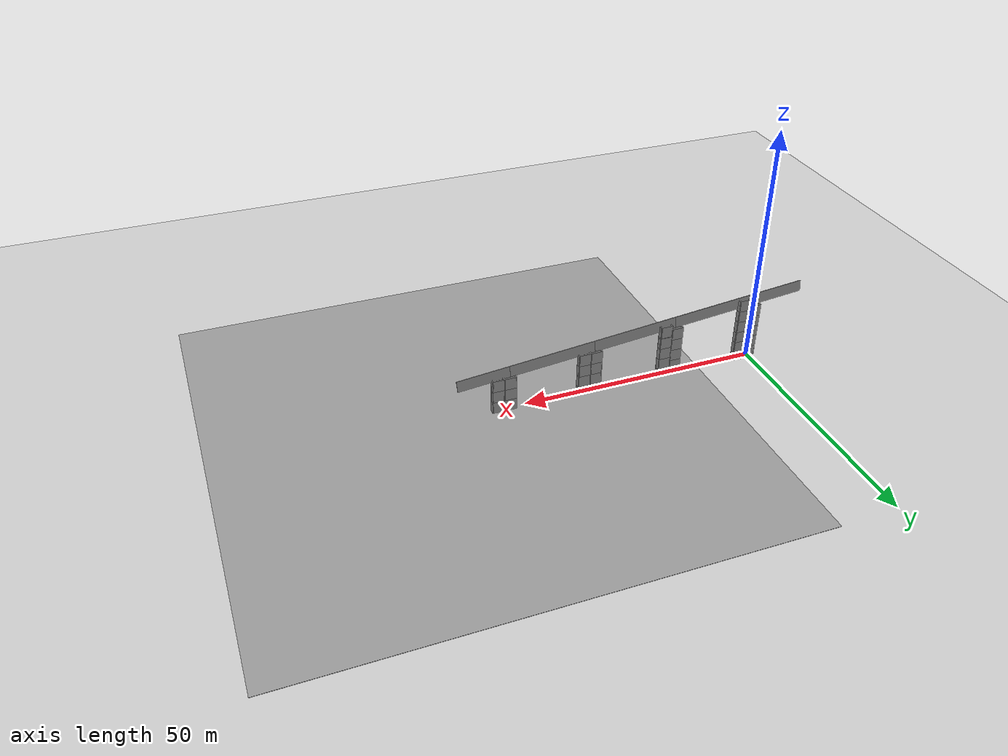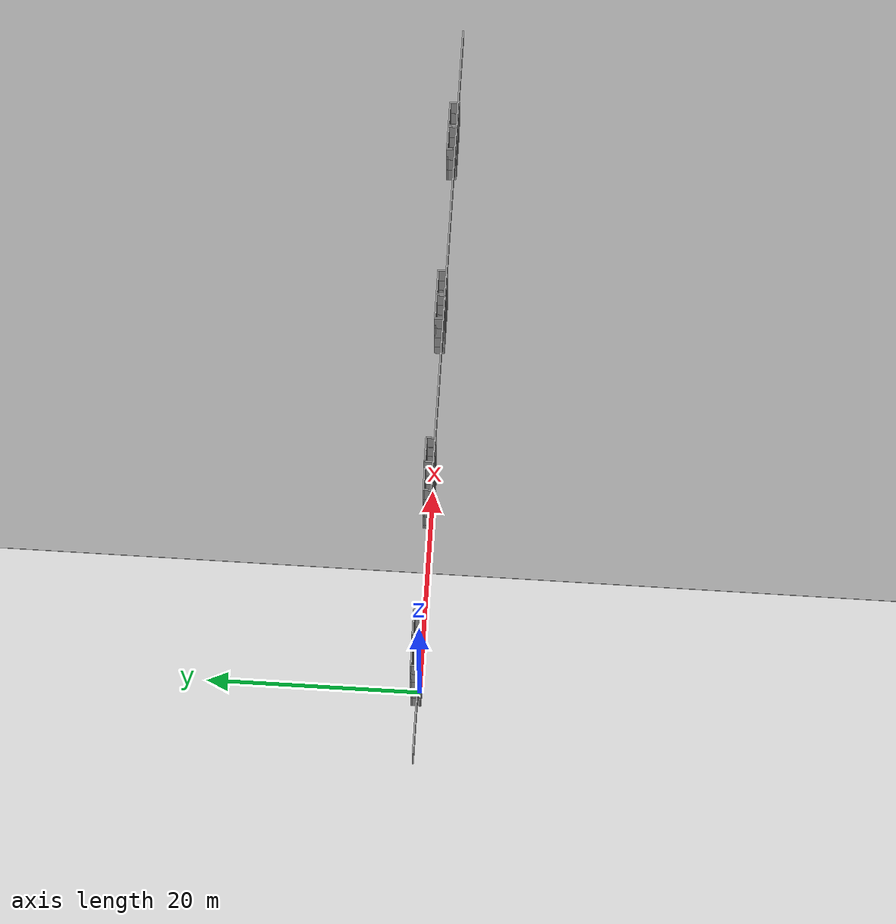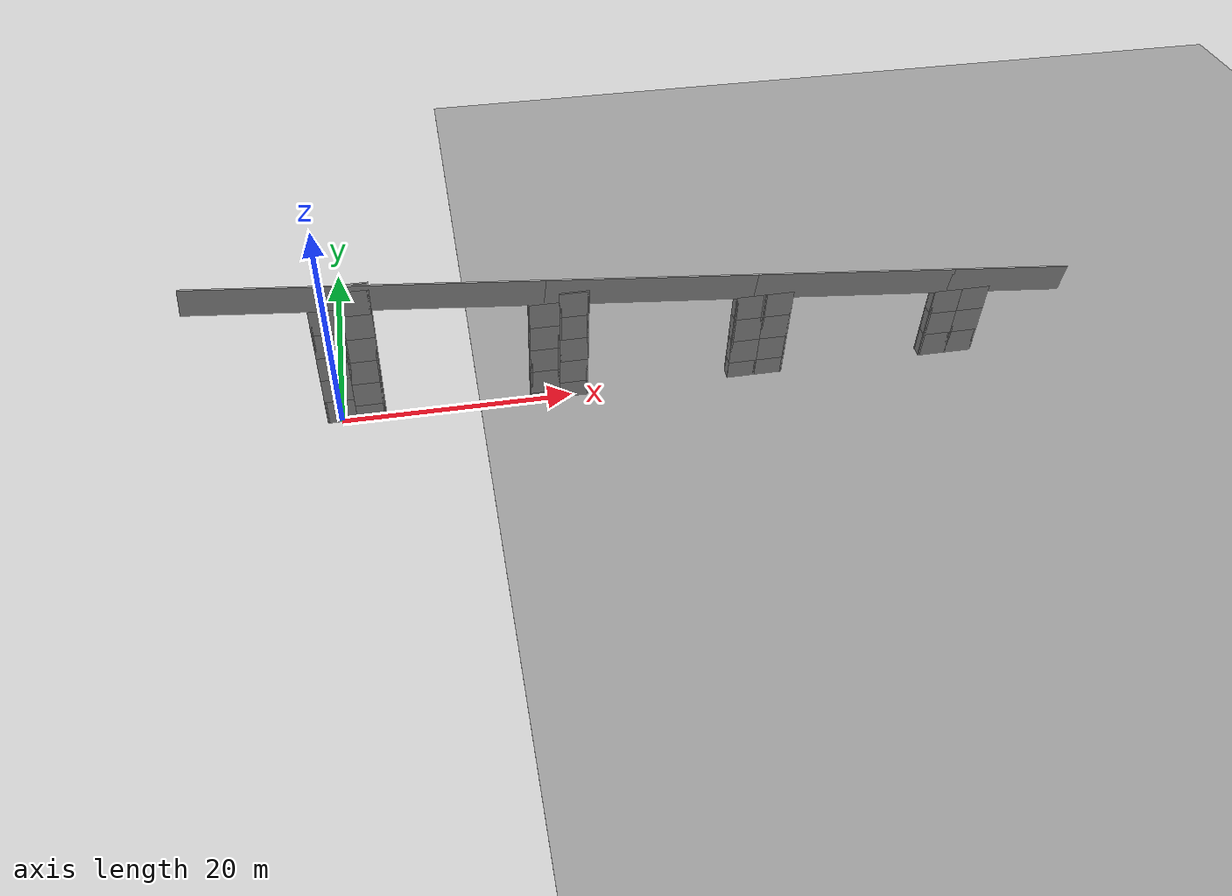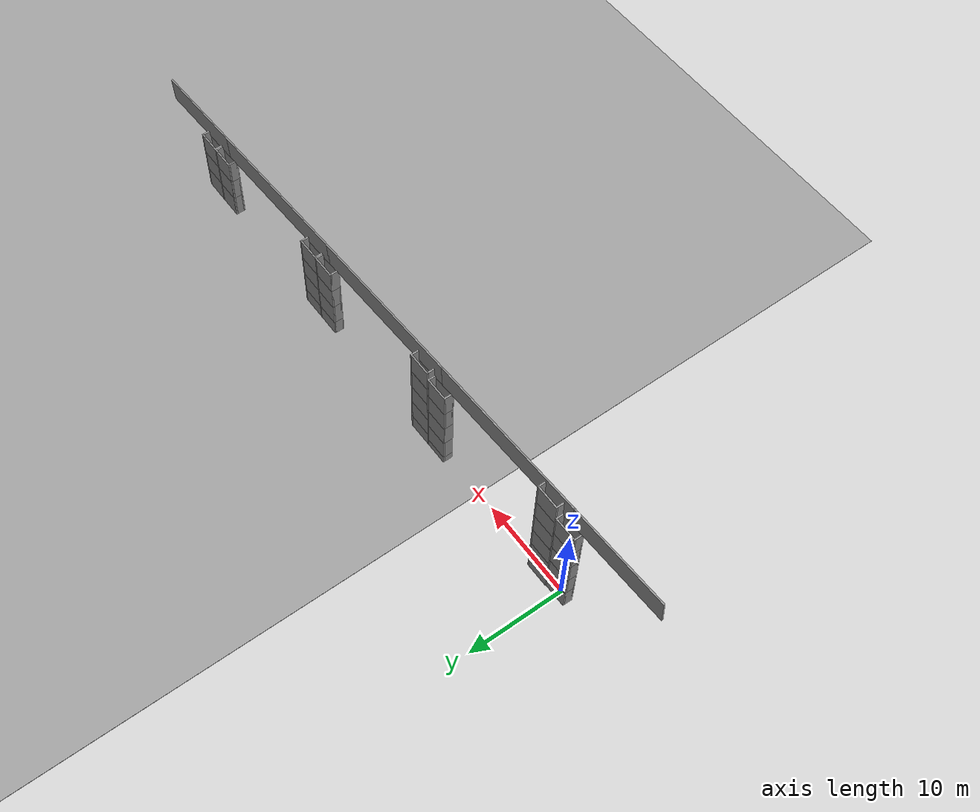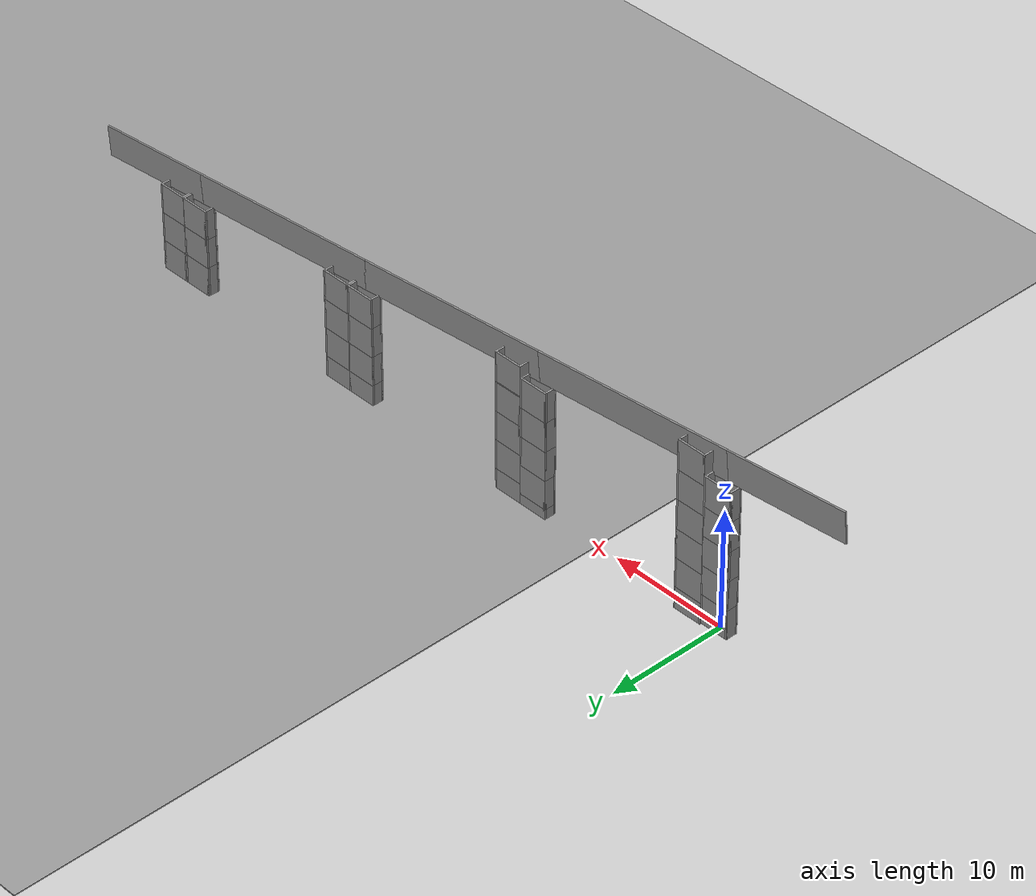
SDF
<sdf version="1.6">
 <world name="default">
  <light name="sun" type="directional">
   <pose>0 0 10 0 -0 0</pose>
   <diffuse>0.8 0.8 0.8 1</diffuse>
   <specular>0.1 0.1 0.1 1</specular>
   <attenuation>
    <range>1000</range>
    <constant>0.9</constant>
    <linear>0.01</linear>
    <quadratic>0.001</quadratic>
   </attenuation>
   <direction>-0.5 0.5 -1</direction>
  </light>
  <model name="ground_plane">
   <static>1</static>
   <link name="link">
    <collision name="collision">
     <geometry><plane><normal>0 0 1</normal><size>100 100</size></plane></geometry>
     <surface><friction><ode><mu>100</mu><mu2>50</mu2></ode></friction></surface>
    </collision>
    <visual name="visual">
     <cast_shadows>0</cast_shadows>
     <geometry><plane><normal>0 0 1</normal><size>100 100</size></plane></geometry>
     <material>
      <script><uri>file://media/materials/scripts/gazebo.material</uri><name>Gazebo/Grey</name></script>
     </material>
    </visual>
   </link>
  </model>
  <gravity>0 0 -9.8</gravity>
  <magnetic_field>6e-06 2.3e-05 -4.2e-05</magnetic_field>
  <atmosphere type="adiabatic"/>
  <physics name="default_physics" default="0" type="ode">
   <max_step_size>0.001</max_step_size>
   <real_time_factor>1</real_time_factor>
   <real_time_update_rate>1000</real_time_update_rate>
  </physics>
  <scene><ambient>0.4 0.4 0.4 1</ambient><background>0.7 0.7 0.7 1</background><shadows>1</shadows></scene>
  <spherical_coordinates>
   <surface_model>EARTH_WGS84</surface_model>
   <latitude_deg>0</latitude_deg>
   <longitude_deg>0</longitude_deg>
   <elevation>0</elevation>
   <heading_deg>0</heading_deg>
  </spherical_coordinates>
  <model name="girder8th">
   <pose>26.53 -0.080607 9.9346 0 0.096041 0</pose>
   <link name="Wall_15">
    <collision name="Wall_15_Collision">
     <geometry><box><size>18 0.15 2.5</size></box></geometry>
     <pose>0 0 1.25 0 -0 0</pose>
    </collision>
    <visual name="Wall_15_Visual">
     <pose>0 0 1.25 0 -0 0</pose>
     <geometry><box><size>18 0.15 2.5</size></box></geometry>
     <material>
      <script><uri>file://media/materials/scripts/gazebo.material</uri><name>Gazebo/Grey</name></script>
      <ambient>1 1 1 1</ambient>
     </material>
    </visual>
    <pose>-17.85 0 0 0 -0 0</pose>
   </link>
   <link name="Wall_17">
    <collision name="Wall_17_Collision">
     <geometry><box><size>18 0.15 2.5</size></box></geometry>
     <pose>0 0 1.25 0 -0 0</pose>
    </collision>
    <visual name="Wall_17_Visual">
     <pose>0 0 1.25 0 -0 0</pose>
     <geometry><box><size>18 0.15 2.5</size></box></geometry>
     <material>
      <script><uri>file://media/materials/scripts/gazebo.material</uri><name>Gazebo/Grey</name></script>
      <ambient>1 1 1 1</ambient>
     </material>
    </visual>
   </link>
   <link name="Wall_19">
    <collision name="Wall_19_Collision">
     <geometry><box><size>18 0.15 2.5</size></box></geometry>
     <pose>0 0 1.25 0 -0 0</pose>
    </collision>
    <visual name="Wall_19_Visual">
     <pose>0 0 1.25 0 -0 0</pose>
     <geometry><box><size>18 0.15 2.5</size></box></geometry>
     <material>
      <script><uri>file://media/materials/scripts/gazebo.material</uri><name>Gazebo/Grey</name></script>
      <ambient>1 1 1 1</ambient>
     </material>
    </visual>
    <pose>17.85 0 0 0 -0 0</pose>
   </link>
   <link name="Wall_21">
    <collision name="Wall_21_Collision">
     <geometry><box><size>10.8 0.15 2.5</size></box></geometry>
     <pose>0 0 1.25 0 -0 0</pose>
    </collision>
    <visual name="Wall_21_Visual">
     <pose>0 0 1.25 0 -0 0</pose>
     <geometry><box><size>10.8 0.15 2.5</size></box></geometry>
     <material>
      <script><uri>file://media/materials/scripts/gazebo.material</uri><name>Gazebo/Grey</name></script>
      <ambient>1 1 1 1</ambient>
     </material>
    </visual>
    <pose>32.1 0 0 0 -0 0</pose>
   </link>
   <link name="Wall_9">
    <collision name="Wall_9_Collision">
     <geometry><box><size>10.8 0.15 2.5</size></box></geometry>
     <pose>0 0 1.25 0 -0 0</pose>
    </collision>
    <visual name="Wall_9_Visual">
     <pose>0 0 1.25 0 -0 0</pose>
     <geometry><box><size>10.8 0.15 2.5</size></box></geometry>
     <material>
      <script><uri>file://media/materials/scripts/gazebo.material</uri><name>Gazebo/Grey</name></script>
      <ambient>1 1 1 1</ambient>
     </material>
    </visual>
    <pose>-32.1 0 0 0 -0 0</pose>
   </link>
   <static>1</static>
  </model>
  <model name="ground_plane_0">
   <static>1</static>
   <link name="link">
    <collision name="collision">
     <geometry><plane><normal>0 0 1</normal><size>100 100</size></plane></geometry>
     <surface>
      <contact><collide_bitmask>65535</collide_bitmask></contact>
      <friction><ode><mu>100</mu><mu2>50</mu2></ode></friction>
     </surface>
    </collision>
    <visual name="visual">
     <cast_shadows>0</cast_shadows>
     <geometry><plane><normal>0 0 1</normal><size>100 100</size></plane></geometry>
     <material>
      <script><uri>file://media/materials/scripts/gazebo.material</uri><name>Gazebo/Grey</name></script>
     </material>
    </visual>
   </link>
   <pose>61.8728 0.736212 0 0 -0 0</pose>
  </model>
  <model name="column25">
   <pose>-0.023775 0.294916 10.1143 0 -0 0</pose>
   <link name="Wall_0">
    <collision name="Wall_0_Collision">
     <geometry><box><size>2.5 0.15 2.5</size></box></geometry>
     <pose>0 0 1.25 0 -0 0</pose>
    </collision>
    <visual name="Wall_0_Visual">
     <pose>0 0 1.25 0 -0 0</pose>
     <geometry><box><size>2.5 0.15 2.5</size></box></geometry>
     <material>
      <script><uri>file://media/materials/scripts/gazebo.material</uri><name>Gazebo/Grey</name></script>
      <ambient>1 1 1 1</ambient>
     </material>
    </visual>
    <pose>0 -0.425 0 0 -0 0</pose>
   </link>
   <link name="Wall_1">
    <collision name="Wall_1_Collision">
     <geometry><box><size>1 0.15 2.5</size></box></geometry>
     <pose>0 0 1.25 0 -0 0</pose>
    </collision>
    <visual name="Wall_1_Visual">
     <pose>0 0 1.25 0 -0 0</pose>
     <geometry><box><size>1 0.15 2.5</size></box></geometry>
     <material>
      <script><uri>file://media/materials/scripts/gazebo.material</uri><name>Gazebo/Grey</name></script>
      <ambient>1 1 1 1</ambient>
     </material>
    </visual>
    <pose>1.175 0 0 0 -0 1.5708</pose>
   </link>
   <link name="Wall_2">
    <collision name="Wall_2_Collision">
     <geometry><box><size>2.5 0.15 2.5</size></box></geometry>
     <pose>0 0 1.25 0 -0 0</pose>
    </collision>
    <visual name="Wall_2_Visual">
     <pose>0 0 1.25 0 -0 0</pose>
     <geometry><box><size>2.5 0.15 2.5</size></box></geometry>
     <material>
      <script><uri>file://media/materials/scripts/gazebo.material</uri><name>Gazebo/Grey</name></script>
      <ambient>1 1 1 1</ambient>
     </material>
    </visual>
    <pose>0 0.425 0 0 -0 3.14159</pose>
   </link>
   <link name="Wall_3">
    <collision name="Wall_3_Collision">
     <geometry><box><size>1 0.15 2.5</size></box></geometry>
     <pose>0 0 1.25 0 -0 0</pose>
    </collision>
    <visual name="Wall_3_Visual">
     <pose>0 0 1.25 0 -0 0</pose>
     <geometry><box><size>1 0.15 2.5</size></box></geometry>
     <material>
      <script><uri>file://media/materials/scripts/gazebo.material</uri><name>Gazebo/Grey</name></script>
      <ambient>1 1 1 1</ambient>
     </material>
    </visual>
    <pose>-1.175 0 0 0 0 -1.5708</pose>
   </link>
   <static>1</static>
  </model>
  <model name="column25_clone">
   <pose>-0.023775 0.294916 7.61428 0 -0 0</pose>
   <link name="Wall_0">
    <collision name="Wall_0_Collision">
     <geometry><box><size>2.5 0.15 2.5</size></box></geometry>
     <pose>0 0 1.25 0 -0 0</pose>
    </collision>
    <visual name="Wall_0_Visual">
     <pose>0 0 1.25 0 -0 0</pose>
     <geometry><box><size>2.5 0.15 2.5</size></box></geometry>
     <material>
      <script><uri>file://media/materials/scripts/gazebo.material</uri><name>Gazebo/Grey</name></script>
      <ambient>1 1 1 1</ambient>
     </material>
    </visual>
    <pose>0 -0.425 0 0 -0 0</pose>
   </link>
   <link name="Wall_1">
    <collision name="Wall_1_Collision">
     <geometry><box><size>1 0.15 2.5</size></box></geometry>
     <pose>0 0 1.25 0 -0 0</pose>
    </collision>
    <visual name="Wall_1_Visual">
     <pose>0 0 1.25 0 -0 0</pose>
     <geometry><box><size>1 0.15 2.5</size></box></geometry>
     <material>
      <script><uri>file://media/materials/scripts/gazebo.material</uri><name>Gazebo/Grey</name></script>
      <ambient>1 1 1 1</ambient>
     </material>
    </visual>
    <pose>1.175 0 0 0 -0 1.5708</pose>
   </link>
   <link name="Wall_2">
    <collision name="Wall_2_Collision">
     <geometry><box><size>2.5 0.15 2.5</size></box></geometry>
     <pose>0 0 1.25 0 -0 0</pose>
    </collision>
    <visual name="Wall_2_Visual">
     <pose>0 0 1.25 0 -0 0</pose>
     <geometry><box><size>2.5 0.15 2.5</size></box></geometry>
     <material>
      <script><uri>file://media/materials/scripts/gazebo.material</uri><name>Gazebo/Grey</name></script>
      <ambient>1 1 1 1</ambient>
     </material>
    </visual>
    <pose>0 0.425 0 0 -0 3.14159</pose>
   </link>
   <link name="Wall_3">
    <collision name="Wall_3_Collision">
     <geometry><box><size>1 0.15 2.5</size></box></geometry>
     <pose>0 0 1.25 0 -0 0</pose>
    </collision>
    <visual name="Wall_3_Visual">
     <pose>0 0 1.25 0 -0 0</pose>
     <geometry><box><size>1 0.15 2.5</size></box></geometry>
     <material>
      <script><uri>file://media/materials/scripts/gazebo.material</uri><name>Gazebo/Grey</name></script>
      <ambient>1 1 1 1</ambient>
     </material>
    </visual>
    <pose>-1.175 0 0 0 0 -1.5708</pose>
   </link>
   <static>1</static>
  </model>
  <model name="column25_clone_0">
   <pose>-0.023776 0.294916 5.11428 0 -0 0</pose>
   <link name="Wall_0">
    <collision name="Wall_0_Collision">
     <geometry><box><size>2.5 0.15 2.5</size></box></geometry>
     <pose>0 0 1.25 0 -0 0</pose>
    </collision>
    <visual name="Wall_0_Visual">
     <pose>0 0 1.25 0 -0 0</pose>
     <geometry><box><size>2.5 0.15 2.5</size></box></geometry>
     <material>
      <script><uri>file://media/materials/scripts/gazebo.material</uri><name>Gazebo/Grey</name></script>
      <ambient>1 1 1 1</ambient>
     </material>
    </visual>
    <pose>0 -0.425 0 0 -0 0</pose>
   </link>
   <link name="Wall_1">
    <collision name="Wall_1_Collision">
     <geometry><box><size>1 0.15 2.5</size></box></geometry>
     <pose>0 0 1.25 0 -0 0</pose>
    </collision>
    <visual name="Wall_1_Visual">
     <pose>0 0 1.25 0 -0 0</pose>
     <geometry><box><size>1 0.15 2.5</size></box></geometry>
     <material>
      <script><uri>file://media/materials/scripts/gazebo.material</uri><name>Gazebo/Grey</name></script>
      <ambient>1 1 1 1</ambient>
     </material>
    </visual>
    <pose>1.175 0 0 0 -0 1.5708</pose>
   </link>
   <link name="Wall_2">
    <collision name="Wall_2_Collision">
     <geometry><box><size>2.5 0.15 2.5</size></box></geometry>
     <pose>0 0 1.25 0 -0 0</pose>
    </collision>
    <visual name="Wall_2_Visual">
     <pose>0 0 1.25 0 -0 0</pose>
     <geometry><box><size>2.5 0.15 2.5</size></box></geometry>
     <material>
      <script><uri>file://media/materials/scripts/gazebo.material</uri><name>Gazebo/Grey</name></script>
      <ambient>1 1 1 1</ambient>
     </material>
    </visual>
    <pose>0 0.425 0 0 -0 3.14159</pose>
   </link>
   <link name="Wall_3">
    <collision name="Wall_3_Collision">
     <geometry><box><size>1 0.15 2.5</size></box></geometry>
     <pose>0 0 1.25 0 -0 0</pose>
    </collision>
    <visual name="Wall_3_Visual">
     <pose>0 0 1.25 0 -0 0</pose>
     <geometry><box><size>1 0.15 2.5</size></box></geometry>
     <material>
      <script><uri>file://media/materials/scripts/gazebo.material</uri><name>Gazebo/Grey</name></script>
      <ambient>1 1 1 1</ambient>
     </material>
    </visual>
    <pose>-1.175 0 0 0 0 -1.5708</pose>
   </link>
   <static>1</static>
  </model>
  <model name="column25_clone_1">
   <pose>-0.023776 0.294916 2.61428 0 -0 0</pose>
   <link name="Wall_0">
    <collision name="Wall_0_Collision">
     <geometry><box><size>2.5 0.15 2.5</size></box></geometry>
     <pose>0 0 1.25 0 -0 0</pose>
    </collision>
    <visual name="Wall_0_Visual">
     <pose>0 0 1.25 0 -0 0</pose>
     <geometry><box><size>2.5 0.15 2.5</size></box></geometry>
     <material>
      <script><uri>file://media/materials/scripts/gazebo.material</uri><name>Gazebo/Grey</name></script>
      <ambient>1 1 1 1</ambient>
     </material>
    </visual>
    <pose>0 -0.425 0 0 -0 0</pose>
   </link>
   <link name="Wall_1">
    <collision name="Wall_1_Collision">
     <geometry><box><size>1 0.15 2.5</size></box></geometry>
     <pose>0 0 1.25 0 -0 0</pose>
    </collision>
    <visual name="Wall_1_Visual">
     <pose>0 0 1.25 0 -0 0</pose>
     <geometry><box><size>1 0.15 2.5</size></box></geometry>
     <material>
      <script><uri>file://media/materials/scripts/gazebo.material</uri><name>Gazebo/Grey</name></script>
      <ambient>1 1 1 1</ambient>
     </material>
    </visual>
    <pose>1.175 0 0 0 -0 1.5708</pose>
   </link>
   <link name="Wall_2">
    <collision name="Wall_2_Collision">
     <geometry><box><size>2.5 0.15 2.5</size></box></geometry>
     <pose>0 0 1.25 0 -0 0</pose>
    </collision>
    <visual name="Wall_2_Visual">
     <pose>0 0 1.25 0 -0 0</pose>
     <geometry><box><size>2.5 0.15 2.5</size></box></geometry>
     <material>
      <script><uri>file://media/materials/scripts/gazebo.material</uri><name>Gazebo/Grey</name></script>
      <ambient>1 1 1 1</ambient>
     </material>
    </visual>
    <pose>0 0.425 0 0 -0 3.14159</pose>
   </link>
   <link name="Wall_3">
    <collision name="Wall_3_Collision">
     <geometry><box><size>1 0.15 2.5</size></box></geometry>
     <pose>0 0 1.25 0 -0 0</pose>
    </collision>
    <visual name="Wall_3_Visual">
     <pose>0 0 1.25 0 -0 0</pose>
     <geometry><box><size>1 0.15 2.5</size></box></geometry>
     <material>
      <script><uri>file://media/materials/scripts/gazebo.material</uri><name>Gazebo/Grey</name></script>
      <ambient>1 1 1 1</ambient>
     </material>
    </visual>
    <pose>-1.175 0 0 0 0 -1.5708</pose>
   </link>
   <static>1</static>
  </model>
  <model name="column25_clone_2">
   <pose>-0.023776 0.294916 0.114275 0 -0 0</pose>
   <link name="Wall_0">
    <collision name="Wall_0_Collision">
     <geometry><box><size>2.5 0.15 2.5</size></box></geometry>
     <pose>0 0 1.25 0 -0 0</pose>
    </collision>
    <visual name="Wall_0_Visual">
     <pose>0 0 1.25 0 -0 0</pose>
     <geometry><box><size>2.5 0.15 2.5</size></box></geometry>
     <material>
      <script><uri>file://media/materials/scripts/gazebo.material</uri><name>Gazebo/Grey</name></script>
      <ambient>1 1 1 1</ambient>
     </material>
    </visual>
    <pose>0 -0.425 0 0 -0 0</pose>
   </link>
   <link name="Wall_1">
    <collision name="Wall_1_Collision">
     <geometry><box><size>1 0.15 2.5</size></box></geometry>
     <pose>0 0 1.25 0 -0 0</pose>
    </collision>
    <visual name="Wall_1_Visual">
     <pose>0 0 1.25 0 -0 0</pose>
     <geometry><box><size>1 0.15 2.5</size></box></geometry>
     <material>
      <script><uri>file://media/materials/scripts/gazebo.material</uri><name>Gazebo/Grey</name></script>
      <ambient>1 1 1 1</ambient>
     </material>
    </visual>
    <pose>1.175 0 0 0 -0 1.5708</pose>
   </link>
   <link name="Wall_2">
    <collision name="Wall_2_Collision">
     <geometry><box><size>2.5 0.15 2.5</size></box></geometry>
     <pose>0 0 1.25 0 -0 0</pose>
    </collision>
    <visual name="Wall_2_Visual">
     <pose>0 0 1.25 0 -0 0</pose>
     <geometry><box><size>2.5 0.15 2.5</size></box></geometry>
     <material>
      <script><uri>file://media/materials/scripts/gazebo.material</uri><name>Gazebo/Grey</name></script>
      <ambient>1 1 1 1</ambient>
     </material>
    </visual>
    <pose>0 0.425 0 0 -0 3.14159</pose>
   </link>
   <link name="Wall_3">
    <collision name="Wall_3_Collision">
     <geometry><box><size>1 0.15 2.5</size></box></geometry>
     <pose>0 0 1.25 0 -0 0</pose>
    </collision>
    <visual name="Wall_3_Visual">
     <pose>0 0 1.25 0 -0 0</pose>
     <geometry><box><size>1 0.15 2.5</size></box></geometry>
     <material>
      <script><uri>file://media/materials/scripts/gazebo.material</uri><name>Gazebo/Grey</name></script>
      <ambient>1 1 1 1</ambient>
     </material>
    </visual>
    <pose>-1.175 0 0 0 0 -1.5708</pose>
   </link>
   <static>1</static>
  </model>
  <model name="column25_clone_3">
   <pose>17.6084 0.281952 8.41814 0 -0 0</pose>
   <link name="Wall_0">
    <collision name="Wall_0_Collision">
     <geometry><box><size>2.5 0.15 2.5</size></box></geometry>
     <pose>0 0 1.25 0 -0 0</pose>
    </collision>
    <visual name="Wall_0_Visual">
     <pose>0 0 1.25 0 -0 0</pose>
     <geometry><box><size>2.5 0.15 2.5</size></box></geometry>
     <material>
      <script><uri>file://media/materials/scripts/gazebo.material</uri><name>Gazebo/Grey</name></script>
      <ambient>1 1 1 1</ambient>
     </material>
    </visual>
    <pose>0 -0.425 0 0 -0 0</pose>
   </link>
   <link name="Wall_1">
    <collision name="Wall_1_Collision">
     <geometry><box><size>1 0.15 2.5</size></box></geometry>
     <pose>0 0 1.25 0 -0 0</pose>
    </collision>
    <visual name="Wall_1_Visual">
     <pose>0 0 1.25 0 -0 0</pose>
     <geometry><box><size>1 0.15 2.5</size></box></geometry>
     <material>
      <script><uri>file://media/materials/scripts/gazebo.material</uri><name>Gazebo/Grey</name></script>
      <ambient>1 1 1 1</ambient>
     </material>
    </visual>
    <pose>1.175 0 0 0 -0 1.5708</pose>
   </link>
   <link name="Wall_2">
    <collision name="Wall_2_Collision">
     <geometry><box><size>2.5 0.15 2.5</size></box></geometry>
     <pose>0 0 1.25 0 -0 0</pose>
    </collision>
    <visual name="Wall_2_Visual">
     <pose>0 0 1.25 0 -0 0</pose>
     <geometry><box><size>2.5 0.15 2.5</size></box></geometry>
     <material>
      <script><uri>file://media/materials/scripts/gazebo.material</uri><name>Gazebo/Grey</name></script>
      <ambient>1 1 1 1</ambient>
     </material>
    </visual>
    <pose>0 0.425 0 0 -0 3.14159</pose>
   </link>
   <link name="Wall_3">
    <collision name="Wall_3_Collision">
     <geometry><box><size>1 0.15 2.5</size></box></geometry>
     <pose>0 0 1.25 0 -0 0</pose>
    </collision>
    <visual name="Wall_3_Visual">
     <pose>0 0 1.25 0 -0 0</pose>
     <geometry><box><size>1 0.15 2.5</size></box></geometry>
     <material>
      <script><uri>file://media/materials/scripts/gazebo.material</uri><name>Gazebo/Grey</name></script>
      <ambient>1 1 1 1</ambient>
     </material>
    </visual>
    <pose>-1.175 0 0 0 0 -1.5708</pose>
   </link>
   <static>1</static>
  </model>
  <model name="column25_clone_3_clone">
   <pose>17.6084 0.281952 5.91814 0 -0 0</pose>
   <link name="Wall_0">
    <collision name="Wall_0_Collision">
     <geometry><box><size>2.5 0.15 2.5</size></box></geometry>
     <pose>0 0 1.25 0 -0 0</pose>
    </collision>
    <visual name="Wall_0_Visual">
     <pose>0 0 1.25 0 -0 0</pose>
     <geometry><box><size>2.5 0.15 2.5</size></box></geometry>
     <material>
      <script><uri>file://media/materials/scripts/gazebo.material</uri><name>Gazebo/Grey</name></script>
      <ambient>1 1 1 1</ambient>
     </material>
    </visual>
    <pose>0 -0.425 0 0 -0 0</pose>
   </link>
   <link name="Wall_1">
    <collision name="Wall_1_Collision">
     <geometry><box><size>1 0.15 2.5</size></box></geometry>
     <pose>0 0 1.25 0 -0 0</pose>
    </collision>
    <visual name="Wall_1_Visual">
     <pose>0 0 1.25 0 -0 0</pose>
     <geometry><box><size>1 0.15 2.5</size></box></geometry>
     <material>
      <script><uri>file://media/materials/scripts/gazebo.material</uri><name>Gazebo/Grey</name></script>
      <ambient>1 1 1 1</ambient>
     </material>
    </visual>
    <pose>1.175 0 0 0 -0 1.5708</pose>
   </link>
   <link name="Wall_2">
    <collision name="Wall_2_Collision">
     <geometry><box><size>2.5 0.15 2.5</size></box></geometry>
     <pose>0 0 1.25 0 -0 0</pose>
    </collision>
    <visual name="Wall_2_Visual">
     <pose>0 0 1.25 0 -0 0</pose>
     <geometry><box><size>2.5 0.15 2.5</size></box></geometry>
     <material>
      <script><uri>file://media/materials/scripts/gazebo.material</uri><name>Gazebo/Grey</name></script>
      <ambient>1 1 1 1</ambient>
     </material>
    </visual>
    <pose>0 0.425 0 0 -0 3.14159</pose>
   </link>
   <link name="Wall_3">
    <collision name="Wall_3_Collision">
     <geometry><box><size>1 0.15 2.5</size></box></geometry>
     <pose>0 0 1.25 0 -0 0</pose>
    </collision>
    <visual name="Wall_3_Visual">
     <pose>0 0 1.25 0 -0 0</pose>
     <geometry><box><size>1 0.15 2.5</size></box></geometry>
     <material>
      <script><uri>file://media/materials/scripts/gazebo.material</uri><name>Gazebo/Grey</name></script>
      <ambient>1 1 1 1</ambient>
     </material>
    </visual>
    <pose>-1.175 0 0 0 0 -1.5708</pose>
   </link>
   <static>1</static>
  </model>
  <model name="column25_clone_3_clone_clone">
   <pose>17.6084 0.281952 3.41814 0 -0 0</pose>
   <link name="Wall_0">
    <collision name="Wall_0_Collision">
     <geometry><box><size>2.5 0.15 2.5</size></box></geometry>
     <pose>0 0 1.25 0 -0 0</pose>
    </collision>
    <visual name="Wall_0_Visual">
     <pose>0 0 1.25 0 -0 0</pose>
     <geometry><box><size>2.5 0.15 2.5</size></box></geometry>
     <material>
      <script><uri>file://media/materials/scripts/gazebo.material</uri><name>Gazebo/Grey</name></script>
      <ambient>1 1 1 1</ambient>
     </material>
    </visual>
    <pose>0 -0.425 0 0 -0 0</pose>
   </link>
   <link name="Wall_1">
    <collision name="Wall_1_Collision">
     <geometry><box><size>1 0.15 2.5</size></box></geometry>
     <pose>0 0 1.25 0 -0 0</pose>
    </collision>
    <visual name="Wall_1_Visual">
     <pose>0 0 1.25 0 -0 0</pose>
     <geometry><box><size>1 0.15 2.5</size></box></geometry>
     <material>
      <script><uri>file://media/materials/scripts/gazebo.material</uri><name>Gazebo/Grey</name></script>
      <ambient>1 1 1 1</ambient>
     </material>
    </visual>
    <pose>1.175 0 0 0 -0 1.5708</pose>
   </link>
   <link name="Wall_2">
    <collision name="Wall_2_Collision">
     <geometry><box><size>2.5 0.15 2.5</size></box></geometry>
     <pose>0 0 1.25 0 -0 0</pose>
    </collision>
    <visual name="Wall_2_Visual">
     <pose>0 0 1.25 0 -0 0</pose>
     <geometry><box><size>2.5 0.15 2.5</size></box></geometry>
     <material>
      <script><uri>file://media/materials/scripts/gazebo.material</uri><name>Gazebo/Grey</name></script>
      <ambient>1 1 1 1</ambient>
     </material>
    </visual>
    <pose>0 0.425 0 0 -0 3.14159</pose>
   </link>
   <link name="Wall_3">
    <collision name="Wall_3_Collision">
     <geometry><box><size>1 0.15 2.5</size></box></geometry>
     <pose>0 0 1.25 0 -0 0</pose>
    </collision>
    <visual name="Wall_3_Visual">
     <pose>0 0 1.25 0 -0 0</pose>
     <geometry><box><size>1 0.15 2.5</size></box></geometry>
     <material>
      <script><uri>file://media/materials/scripts/gazebo.material</uri><name>Gazebo/Grey</name></script>
      <ambient>1 1 1 1</ambient>
     </material>
    </visual>
    <pose>-1.175 0 0 0 0 -1.5708</pose>
   </link>
   <static>1</static>
  </model>
  <model name="column25_clone_3_clone_clone_0">
   <pose>17.6084 0.281952 0.918144 0 -0 0</pose>
   <link name="Wall_0">
    <collision name="Wall_0_Collision">
     <geometry><box><size>2.5 0.15 2.5</size></box></geometry>
     <pose>0 0 1.25 0 -0 0</pose>
    </collision>
    <visual name="Wall_0_Visual">
     <pose>0 0 1.25 0 -0 0</pose>
     <geometry><box><size>2.5 0.15 2.5</size></box></geometry>
     <material>
      <script><uri>file://media/materials/scripts/gazebo.material</uri><name>Gazebo/Grey</name></script>
      <ambient>1 1 1 1</ambient>
     </material>
    </visual>
    <pose>0 -0.425 0 0 -0 0</pose>
   </link>
   <link name="Wall_1">
    <collision name="Wall_1_Collision">
     <geometry><box><size>1 0.15 2.5</size></box></geometry>
     <pose>0 0 1.25 0 -0 0</pose>
    </collision>
    <visual name="Wall_1_Visual">
     <pose>0 0 1.25 0 -0 0</pose>
     <geometry><box><size>1 0.15 2.5</size></box></geometry>
     <material>
      <script><uri>file://media/materials/scripts/gazebo.material</uri><name>Gazebo/Grey</name></script>
      <ambient>1 1 1 1</ambient>
     </material>
    </visual>
    <pose>1.175 0 0 0 -0 1.5708</pose>
   </link>
   <link name="Wall_2">
    <collision name="Wall_2_Collision">
     <geometry><box><size>2.5 0.15 2.5</size></box></geometry>
     <pose>0 0 1.25 0 -0 0</pose>
    </collision>
    <visual name="Wall_2_Visual">
     <pose>0 0 1.25 0 -0 0</pose>
     <geometry><box><size>2.5 0.15 2.5</size></box></geometry>
     <material>
      <script><uri>file://media/materials/scripts/gazebo.material</uri><name>Gazebo/Grey</name></script>
      <ambient>1 1 1 1</ambient>
     </material>
    </visual>
    <pose>0 0.425 0 0 -0 3.14159</pose>
   </link>
   <link name="Wall_3">
    <collision name="Wall_3_Collision">
     <geometry><box><size>1 0.15 2.5</size></box></geometry>
     <pose>0 0 1.25 0 -0 0</pose>
    </collision>
    <visual name="Wall_3_Visual">
     <pose>0 0 1.25 0 -0 0</pose>
     <geometry><box><size>1 0.15 2.5</size></box></geometry>
     <material>
      <script><uri>file://media/materials/scripts/gazebo.material</uri><name>Gazebo/Grey</name></script>
      <ambient>1 1 1 1</ambient>
     </material>
    </visual>
    <pose>-1.175 0 0 0 0 -1.5708</pose>
   </link>
   <static>1</static>
  </model>
  <model name="column25_clone_3_clone_clone_0_clone">
   <pose>17.6084 0.281952 -1.58186 0 -0 0</pose>
   <link name="Wall_0">
    <collision name="Wall_0_Collision">
     <geometry><box><size>2.5 0.15 2.5</size></box></geometry>
     <pose>0 0 1.25 0 -0 0</pose>
    </collision>
    <visual name="Wall_0_Visual">
     <pose>0 0 1.25 0 -0 0</pose>
     <geometry><box><size>2.5 0.15 2.5</size></box></geometry>
     <material>
      <script><uri>file://media/materials/scripts/gazebo.material</uri><name>Gazebo/Grey</name></script>
      <ambient>1 1 1 1</ambient>
     </material>
    </visual>
    <pose>0 -0.425 0 0 -0 0</pose>
   </link>
   <link name="Wall_1">
    <collision name="Wall_1_Collision">
     <geometry><box><size>1 0.15 2.5</size></box></geometry>
     <pose>0 0 1.25 0 -0 0</pose>
    </collision>
    <visual name="Wall_1_Visual">
     <pose>0 0 1.25 0 -0 0</pose>
     <geometry><box><size>1 0.15 2.5</size></box></geometry>
     <material>
      <script><uri>file://media/materials/scripts/gazebo.material</uri><name>Gazebo/Grey</name></script>
      <ambient>1 1 1 1</ambient>
     </material>
    </visual>
    <pose>1.175 0 0 0 -0 1.5708</pose>
   </link>
   <link name="Wall_2">
    <collision name="Wall_2_Collision">
     <geometry><box><size>2.5 0.15 2.5</size></box></geometry>
     <pose>0 0 1.25 0 -0 0</pose>
    </collision>
    <visual name="Wall_2_Visual">
     <pose>0 0 1.25 0 -0 0</pose>
     <geometry><box><size>2.5 0.15 2.5</size></box></geometry>
     <material>
      <script><uri>file://media/materials/scripts/gazebo.material</uri><name>Gazebo/Grey</name></script>
      <ambient>1 1 1 1</ambient>
     </material>
    </visual>
    <pose>0 0.425 0 0 -0 3.14159</pose>
   </link>
   <link name="Wall_3">
    <collision name="Wall_3_Collision">
     <geometry><box><size>1 0.15 2.5</size></box></geometry>
     <pose>0 0 1.25 0 -0 0</pose>
    </collision>
    <visual name="Wall_3_Visual">
     <pose>0 0 1.25 0 -0 0</pose>
     <geometry><box><size>1 0.15 2.5</size></box></geometry>
     <material>
      <script><uri>file://media/materials/scripts/gazebo.material</uri><name>Gazebo/Grey</name></script>
      <ambient>1 1 1 1</ambient>
     </material>
    </visual>
    <pose>-1.175 0 0 0 0 -1.5708</pose>
   </link>
   <static>1</static>
  </model>
  <model name="column25_clone_3_clone_0">
   <pose>35.3237 0.315716 6.81299 0 -0 0</pose>
   <link name="Wall_0">
    <collision name="Wall_0_Collision">
     <geometry><box><size>2.5 0.15 2.5</size></box></geometry>
     <pose>0 0 1.25 0 -0 0</pose>
    </collision>
    <visual name="Wall_0_Visual">
     <pose>0 0 1.25 0 -0 0</pose>
     <geometry><box><size>2.5 0.15 2.5</size></box></geometry>
     <material>
      <script><uri>file://media/materials/scripts/gazebo.material</uri><name>Gazebo/Grey</name></script>
      <ambient>1 1 1 1</ambient>
     </material>
    </visual>
    <pose>0 -0.425 0 0 -0 0</pose>
   </link>
   <link name="Wall_1">
    <collision name="Wall_1_Collision">
     <geometry><box><size>1 0.15 2.5</size></box></geometry>
     <pose>0 0 1.25 0 -0 0</pose>
    </collision>
    <visual name="Wall_1_Visual">
     <pose>0 0 1.25 0 -0 0</pose>
     <geometry><box><size>1 0.15 2.5</size></box></geometry>
     <material>
      <script><uri>file://media/materials/scripts/gazebo.material</uri><name>Gazebo/Grey</name></script>
      <ambient>1 1 1 1</ambient>
     </material>
    </visual>
    <pose>1.175 0 0 0 -0 1.5708</pose>
   </link>
   <link name="Wall_2">
    <collision name="Wall_2_Collision">
     <geometry><box><size>2.5 0.15 2.5</size></box></geometry>
     <pose>0 0 1.25 0 -0 0</pose>
    </collision>
    <visual name="Wall_2_Visual">
     <pose>0 0 1.25 0 -0 0</pose>
     <geometry><box><size>2.5 0.15 2.5</size></box></geometry>
     <material>
      <script><uri>file://media/materials/scripts/gazebo.material</uri><name>Gazebo/Grey</name></script>
      <ambient>1 1 1 1</ambient>
     </material>
    </visual>
    <pose>0 0.425 0 0 -0 3.14159</pose>
   </link>
   <link name="Wall_3">
    <collision name="Wall_3_Collision">
     <geometry><box><size>1 0.15 2.5</size></box></geometry>
     <pose>0 0 1.25 0 -0 0</pose>
    </collision>
    <visual name="Wall_3_Visual">
     <pose>0 0 1.25 0 -0 0</pose>
     <geometry><box><size>1 0.15 2.5</size></box></geometry>
     <material>
      <script><uri>file://media/materials/scripts/gazebo.material</uri><name>Gazebo/Grey</name></script>
      <ambient>1 1 1 1</ambient>
     </material>
    </visual>
    <pose>-1.175 0 0 0 0 -1.5708</pose>
   </link>
   <static>1</static>
  </model>
  <model name="column25_clone_3_clone_0_clone">
   <pose>35.3237 0.315716 4.31299 0 -0 0</pose>
   <link name="Wall_0">
    <collision name="Wall_0_Collision">
     <geometry><box><size>2.5 0.15 2.5</size></box></geometry>
     <pose>0 0 1.25 0 -0 0</pose>
    </collision>
    <visual name="Wall_0_Visual">
     <pose>0 0 1.25 0 -0 0</pose>
     <geometry><box><size>2.5 0.15 2.5</size></box></geometry>
     <material>
      <script><uri>file://media/materials/scripts/gazebo.material</uri><name>Gazebo/Grey</name></script>
      <ambient>1 1 1 1</ambient>
     </material>
    </visual>
    <pose>0 -0.425 0 0 -0 0</pose>
   </link>
   <link name="Wall_1">
    <collision name="Wall_1_Collision">
     <geometry><box><size>1 0.15 2.5</size></box></geometry>
     <pose>0 0 1.25 0 -0 0</pose>
    </collision>
    <visual name="Wall_1_Visual">
     <pose>0 0 1.25 0 -0 0</pose>
     <geometry><box><size>1 0.15 2.5</size></box></geometry>
     <material>
      <script><uri>file://media/materials/scripts/gazebo.material</uri><name>Gazebo/Grey</name></script>
      <ambient>1 1 1 1</ambient>
     </material>
    </visual>
    <pose>1.175 0 0 0 -0 1.5708</pose>
   </link>
   <link name="Wall_2">
    <collision name="Wall_2_Collision">
     <geometry><box><size>2.5 0.15 2.5</size></box></geometry>
     <pose>0 0 1.25 0 -0 0</pose>
    </collision>
    <visual name="Wall_2_Visual">
     <pose>0 0 1.25 0 -0 0</pose>
     <geometry><box><size>2.5 0.15 2.5</size></box></geometry>
     <material>
      <script><uri>file://media/materials/scripts/gazebo.material</uri><name>Gazebo/Grey</name></script>
      <ambient>1 1 1 1</ambient>
     </material>
    </visual>
    <pose>0 0.425 0 0 -0 3.14159</pose>
   </link>
   <link name="Wall_3">
    <collision name="Wall_3_Collision">
     <geometry><box><size>1 0.15 2.5</size></box></geometry>
     <pose>0 0 1.25 0 -0 0</pose>
    </collision>
    <visual name="Wall_3_Visual">
     <pose>0 0 1.25 0 -0 0</pose>
     <geometry><box><size>1 0.15 2.5</size></box></geometry>
     <material>
      <script><uri>file://media/materials/scripts/gazebo.material</uri><name>Gazebo/Grey</name></script>
      <ambient>1 1 1 1</ambient>
     </material>
    </visual>
    <pose>-1.175 0 0 0 0 -1.5708</pose>
   </link>
   <static>1</static>
  </model>
  <model name="column25_clone_3_clone_0_clone_clone">
   <pose>35.3237 0.315716 1.81299 0 -0 0</pose>
   <link name="Wall_0">
    <collision name="Wall_0_Collision">
     <geometry><box><size>2.5 0.15 2.5</size></box></geometry>
     <pose>0 0 1.25 0 -0 0</pose>
    </collision>
    <visual name="Wall_0_Visual">
     <pose>0 0 1.25 0 -0 0</pose>
     <geometry><box><size>2.5 0.15 2.5</size></box></geometry>
     <material>
      <script><uri>file://media/materials/scripts/gazebo.material</uri><name>Gazebo/Grey</name></script>
      <ambient>1 1 1 1</ambient>
     </material>
    </visual>
    <pose>0 -0.425 0 0 -0 0</pose>
   </link>
   <link name="Wall_1">
    <collision name="Wall_1_Collision">
     <geometry><box><size>1 0.15 2.5</size></box></geometry>
     <pose>0 0 1.25 0 -0 0</pose>
    </collision>
    <visual name="Wall_1_Visual">
     <pose>0 0 1.25 0 -0 0</pose>
     <geometry><box><size>1 0.15 2.5</size></box></geometry>
     <material>
      <script><uri>file://media/materials/scripts/gazebo.material</uri><name>Gazebo/Grey</name></script>
      <ambient>1 1 1 1</ambient>
     </material>
    </visual>
    <pose>1.175 0 0 0 -0 1.5708</pose>
   </link>
   <link name="Wall_2">
    <collision name="Wall_2_Collision">
     <geometry><box><size>2.5 0.15 2.5</size></box></geometry>
     <pose>0 0 1.25 0 -0 0</pose>
    </collision>
    <visual name="Wall_2_Visual">
     <pose>0 0 1.25 0 -0 0</pose>
     <geometry><box><size>2.5 0.15 2.5</size></box></geometry>
     <material>
      <script><uri>file://media/materials/scripts/gazebo.material</uri><name>Gazebo/Grey</name></script>
      <ambient>1 1 1 1</ambient>
     </material>
    </visual>
    <pose>0 0.425 0 0 -0 3.14159</pose>
   </link>
   <link name="Wall_3">
    <collision name="Wall_3_Collision">
     <geometry><box><size>1 0.15 2.5</size></box></geometry>
     <pose>0 0 1.25 0 -0 0</pose>
    </collision>
    <visual name="Wall_3_Visual">
     <pose>0 0 1.25 0 -0 0</pose>
     <geometry><box><size>1 0.15 2.5</size></box></geometry>
     <material>
      <script><uri>file://media/materials/scripts/gazebo.material</uri><name>Gazebo/Grey</name></script>
      <ambient>1 1 1 1</ambient>
     </material>
    </visual>
    <pose>-1.175 0 0 0 0 -1.5708</pose>
   </link>
   <static>1</static>
  </model>
  <model name="column25_clone_3_clone_0_clone_clone_clone">
   <pose>35.3237 0.315716 -0.687008 0 -0 0</pose>
   <link name="Wall_0">
    <collision name="Wall_0_Collision">
     <geometry><box><size>2.5 0.15 2.5</size></box></geometry>
     <pose>0 0 1.25 0 -0 0</pose>
    </collision>
    <visual name="Wall_0_Visual">
     <pose>0 0 1.25 0 -0 0</pose>
     <geometry><box><size>2.5 0.15 2.5</size></box></geometry>
     <material>
      <script><uri>file://media/materials/scripts/gazebo.material</uri><name>Gazebo/Grey</name></script>
      <ambient>1 1 1 1</ambient>
     </material>
    </visual>
    <pose>0 -0.425 0 0 -0 0</pose>
   </link>
   <link name="Wall_1">
    <collision name="Wall_1_Collision">
     <geometry><box><size>1 0.15 2.5</size></box></geometry>
     <pose>0 0 1.25 0 -0 0</pose>
    </collision>
    <visual name="Wall_1_Visual">
     <pose>0 0 1.25 0 -0 0</pose>
     <geometry><box><size>1 0.15 2.5</size></box></geometry>
     <material>
      <script><uri>file://media/materials/scripts/gazebo.material</uri><name>Gazebo/Grey</name></script>
      <ambient>1 1 1 1</ambient>
     </material>
    </visual>
    <pose>1.175 0 0 0 -0 1.5708</pose>
   </link>
   <link name="Wall_2">
    <collision name="Wall_2_Collision">
     <geometry><box><size>2.5 0.15 2.5</size></box></geometry>
     <pose>0 0 1.25 0 -0 0</pose>
    </collision>
    <visual name="Wall_2_Visual">
     <pose>0 0 1.25 0 -0 0</pose>
     <geometry><box><size>2.5 0.15 2.5</size></box></geometry>
     <material>
      <script><uri>file://media/materials/scripts/gazebo.material</uri><name>Gazebo/Grey</name></script>
      <ambient>1 1 1 1</ambient>
     </material>
    </visual>
    <pose>0 0.425 0 0 -0 3.14159</pose>
   </link>
   <link name="Wall_3">
    <collision name="Wall_3_Collision">
     <geometry><box><size>1 0.15 2.5</size></box></geometry>
     <pose>0 0 1.25 0 -0 0</pose>
    </collision>
    <visual name="Wall_3_Visual">
     <pose>0 0 1.25 0 -0 0</pose>
     <geometry><box><size>1 0.15 2.5</size></box></geometry>
     <material>
      <script><uri>file://media/materials/scripts/gazebo.material</uri><name>Gazebo/Grey</name></script>
      <ambient>1 1 1 1</ambient>
     </material>
    </visual>
    <pose>-1.175 0 0 0 0 -1.5708</pose>
   </link>
   <static>1</static>
  </model>
  <model name="column25_clone_3_clone_0_clone_0">
   <pose>53.3565 0.297908 5.07328 0 -0 0</pose>
   <link name="Wall_0">
    <collision name="Wall_0_Collision">
     <geometry><box><size>2.5 0.15 2.5</size></box></geometry>
     <pose>0 0 1.25 0 -0 0</pose>
    </collision>
    <visual name="Wall_0_Visual">
     <pose>0 0 1.25 0 -0 0</pose>
     <geometry><box><size>2.5 0.15 2.5</size></box></geometry>
     <material>
      <script><uri>file://media/materials/scripts/gazebo.material</uri><name>Gazebo/Grey</name></script>
      <ambient>1 1 1 1</ambient>
     </material>
    </visual>
    <pose>0 -0.425 0 0 -0 0</pose>
   </link>
   <link name="Wall_1">
    <collision name="Wall_1_Collision">
     <geometry><box><size>1 0.15 2.5</size></box></geometry>
     <pose>0 0 1.25 0 -0 0</pose>
    </collision>
    <visual name="Wall_1_Visual">
     <pose>0 0 1.25 0 -0 0</pose>
     <geometry><box><size>1 0.15 2.5</size></box></geometry>
     <material>
      <script><uri>file://media/materials/scripts/gazebo.material</uri><name>Gazebo/Grey</name></script>
      <ambient>1 1 1 1</ambient>
     </material>
    </visual>
    <pose>1.175 0 0 0 -0 1.5708</pose>
   </link>
   <link name="Wall_2">
    <collision name="Wall_2_Collision">
     <geometry><box><size>2.5 0.15 2.5</size></box></geometry>
     <pose>0 0 1.25 0 -0 0</pose>
    </collision>
    <visual name="Wall_2_Visual">
     <pose>0 0 1.25 0 -0 0</pose>
     <geometry><box><size>2.5 0.15 2.5</size></box></geometry>
     <material>
      <script><uri>file://media/materials/scripts/gazebo.material</uri><name>Gazebo/Grey</name></script>
      <ambient>1 1 1 1</ambient>
     </material>
    </visual>
    <pose>0 0.425 0 0 -0 3.14159</pose>
   </link>
   <link name="Wall_3">
    <collision name="Wall_3_Collision">
     <geometry><box><size>1 0.15 2.5</size></box></geometry>
     <pose>0 0 1.25 0 -0 0</pose>
    </collision>
    <visual name="Wall_3_Visual">
     <pose>0 0 1.25 0 -0 0</pose>
     <geometry><box><size>1 0.15 2.5</size></box></geometry>
     <material>
      <script><uri>file://media/materials/scripts/gazebo.material</uri><name>Gazebo/Grey</name></script>
      <ambient>1 1 1 1</ambient>
     </material>
    </visual>
    <pose>-1.175 0 0 0 0 -1.5708</pose>
   </link>
   <static>1</static>
  </model>
  <model name="column25_clone_3_clone_0_clone_0_clone">
   <pose>53.3565 0.297908 2.57328 0 -0 0</pose>
   <link name="Wall_0">
    <collision name="Wall_0_Collision">
     <geometry><box><size>2.5 0.15 2.5</size></box></geometry>
     <pose>0 0 1.25 0 -0 0</pose>
    </collision>
    <visual name="Wall_0_Visual">
     <pose>0 0 1.25 0 -0 0</pose>
     <geometry><box><size>2.5 0.15 2.5</size></box></geometry>
     <material>
      <script><uri>file://media/materials/scripts/gazebo.material</uri><name>Gazebo/Grey</name></script>
      <ambient>1 1 1 1</ambient>
     </material>
    </visual>
    <pose>0 -0.425 0 0 -0 0</pose>
   </link>
   <link name="Wall_1">
    <collision name="Wall_1_Collision">
     <geometry><box><size>1 0.15 2.5</size></box></geometry>
     <pose>0 0 1.25 0 -0 0</pose>
    </collision>
    <visual name="Wall_1_Visual">
     <pose>0 0 1.25 0 -0 0</pose>
     <geometry><box><size>1 0.15 2.5</size></box></geometry>
     <material>
      <script><uri>file://media/materials/scripts/gazebo.material</uri><name>Gazebo/Grey</name></script>
      <ambient>1 1 1 1</ambient>
     </material>
    </visual>
    <pose>1.175 0 0 0 -0 1.5708</pose>
   </link>
   <link name="Wall_2">
    <collision name="Wall_2_Collision">
     <geometry><box><size>2.5 0.15 2.5</size></box></geometry>
     <pose>0 0 1.25 0 -0 0</pose>
    </collision>
    <visual name="Wall_2_Visual">
     <pose>0 0 1.25 0 -0 0</pose>
     <geometry><box><size>2.5 0.15 2.5</size></box></geometry>
     <material>
      <script><uri>file://media/materials/scripts/gazebo.material</uri><name>Gazebo/Grey</name></script>
      <ambient>1 1 1 1</ambient>
     </material>
    </visual>
    <pose>0 0.425 0 0 -0 3.14159</pose>
   </link>
   <link name="Wall_3">
    <collision name="Wall_3_Collision">
     <geometry><box><size>1 0.15 2.5</size></box></geometry>
     <pose>0 0 1.25 0 -0 0</pose>
    </collision>
    <visual name="Wall_3_Visual">
     <pose>0 0 1.25 0 -0 0</pose>
     <geometry><box><size>1 0.15 2.5</size></box></geometry>
     <material>
      <script><uri>file://media/materials/scripts/gazebo.material</uri><name>Gazebo/Grey</name></script>
      <ambient>1 1 1 1</ambient>
     </material>
    </visual>
    <pose>-1.175 0 0 0 0 -1.5708</pose>
   </link>
   <static>1</static>
  </model>
  <model name="column25_clone_3_clone_0_clone_0_clone_0">
   <pose>53.3565 0.297908 0.073277 0 -0 0</pose>
   <link name="Wall_0">
    <collision name="Wall_0_Collision">
     <geometry><box><size>2.5 0.15 2.5</size></box></geometry>
     <pose>0 0 1.25 0 -0 0</pose>
    </collision>
    <visual name="Wall_0_Visual">
     <pose>0 0 1.25 0 -0 0</pose>
     <geometry><box><size>2.5 0.15 2.5</size></box></geometry>
     <material>
      <script><uri>file://media/materials/scripts/gazebo.material</uri><name>Gazebo/Grey</name></script>
      <ambient>1 1 1 1</ambient>
     </material>
    </visual>
    <pose>0 -0.425 0 0 -0 0</pose>
   </link>
   <link name="Wall_1">
    <collision name="Wall_1_Collision">
     <geometry><box><size>1 0.15 2.5</size></box></geometry>
     <pose>0 0 1.25 0 -0 0</pose>
    </collision>
    <visual name="Wall_1_Visual">
     <pose>0 0 1.25 0 -0 0</pose>
     <geometry><box><size>1 0.15 2.5</size></box></geometry>
     <material>
      <script><uri>file://media/materials/scripts/gazebo.material</uri><name>Gazebo/Grey</name></script>
      <ambient>1 1 1 1</ambient>
     </material>
    </visual>
    <pose>1.175 0 0 0 -0 1.5708</pose>
   </link>
   <link name="Wall_2">
    <collision name="Wall_2_Collision">
     <geometry><box><size>2.5 0.15 2.5</size></box></geometry>
     <pose>0 0 1.25 0 -0 0</pose>
    </collision>
    <visual name="Wall_2_Visual">
     <pose>0 0 1.25 0 -0 0</pose>
     <geometry><box><size>2.5 0.15 2.5</size></box></geometry>
     <material>
      <script><uri>file://media/materials/scripts/gazebo.material</uri><name>Gazebo/Grey</name></script>
      <ambient>1 1 1 1</ambient>
     </material>
    </visual>
    <pose>0 0.425 0 0 -0 3.14159</pose>
   </link>
   <link name="Wall_3">
    <collision name="Wall_3_Collision">
     <geometry><box><size>1 0.15 2.5</size></box></geometry>
     <pose>0 0 1.25 0 -0 0</pose>
    </collision>
    <visual name="Wall_3_Visual">
     <pose>0 0 1.25 0 -0 0</pose>
     <geometry><box><size>1 0.15 2.5</size></box></geometry>
     <material>
      <script><uri>file://media/materials/scripts/gazebo.material</uri><name>Gazebo/Grey</name></script>
      <ambient>1 1 1 1</ambient>
     </material>
    </visual>
    <pose>-1.175 0 0 0 0 -1.5708</pose>
   </link>
   <static>1</static>
  </model>
  <model name="column25_clone_2_clone">
   <pose>2.47622 0.294925 -0.719058 0 -0 7e-06</pose>
   <link name="Wall_0">
    <collision name="Wall_0_Collision">
     <geometry><box><size>2.5 0.15 2.5</size></box></geometry>
     <pose>0 0 1.25 0 -0 0</pose>
    </collision>
    <visual name="Wall_0_Visual">
     <pose>0 0 1.25 0 -0 0</pose>
     <geometry><box><size>2.5 0.15 2.5</size></box></geometry>
     <material>
      <script><uri>file://media/materials/scripts/gazebo.material</uri><name>Gazebo/Grey</name></script>
      <ambient>1 1 1 1</ambient>
     </material>
    </visual>
    <pose>0 -0.425 0 0 -0 0</pose>
   </link>
   <link name="Wall_1">
    <collision name="Wall_1_Collision">
     <geometry><box><size>1 0.15 2.5</size></box></geometry>
     <pose>0 0 1.25 0 -0 0</pose>
    </collision>
    <visual name="Wall_1_Visual">
     <pose>0 0 1.25 0 -0 0</pose>
     <geometry><box><size>1 0.15 2.5</size></box></geometry>
     <material>
      <script><uri>file://media/materials/scripts/gazebo.material</uri><name>Gazebo/Grey</name></script>
      <ambient>1 1 1 1</ambient>
     </material>
    </visual>
    <pose>1.175 0 0 0 -0 1.5708</pose>
   </link>
   <link name="Wall_2">
    <collision name="Wall_2_Collision">
     <geometry><box><size>2.5 0.15 2.5</size></box></geometry>
     <pose>0 0 1.25 0 -0 0</pose>
    </collision>
    <visual name="Wall_2_Visual">
     <pose>0 0 1.25 0 -0 0</pose>
     <geometry><box><size>2.5 0.15 2.5</size></box></geometry>
     <material>
      <script><uri>file://media/materials/scripts/gazebo.material</uri><name>Gazebo/Grey</name></script>
      <ambient>1 1 1 1</ambient>
     </material>
    </visual>
    <pose>0 0.425 0 0 -0 3.14159</pose>
   </link>
   <link name="Wall_3">
    <collision name="Wall_3_Collision">
     <geometry><box><size>1 0.15 2.5</size></box></geometry>
     <pose>0 0 1.25 0 -0 0</pose>
    </collision>
    <visual name="Wall_3_Visual">
     <pose>0 0 1.25 0 -0 0</pose>
     <geometry><box><size>1 0.15 2.5</size></box></geometry>
     <material>
      <script><uri>file://media/materials/scripts/gazebo.material</uri><name>Gazebo/Grey</name></script>
      <ambient>1 1 1 1</ambient>
     </material>
    </visual>
    <pose>-1.175 0 0 0 0 -1.5708</pose>
   </link>
   <static>1</static>
  </model>
  <model name="column25_clone_2_clone_clone">
   <pose>2.47622 0.294926 1.78094 0 -0 7e-06</pose>
   <link name="Wall_0">
    <collision name="Wall_0_Collision">
     <geometry><box><size>2.5 0.15 2.5</size></box></geometry>
     <pose>0 0 1.25 0 -0 0</pose>
    </collision>
    <visual name="Wall_0_Visual">
     <pose>0 0 1.25 0 -0 0</pose>
     <geometry><box><size>2.5 0.15 2.5</size></box></geometry>
     <material>
      <script><uri>file://media/materials/scripts/gazebo.material</uri><name>Gazebo/Grey</name></script>
      <ambient>1 1 1 1</ambient>
     </material>
    </visual>
    <pose>0 -0.425 0 0 -0 0</pose>
   </link>
   <link name="Wall_1">
    <collision name="Wall_1_Collision">
     <geometry><box><size>1 0.15 2.5</size></box></geometry>
     <pose>0 0 1.25 0 -0 0</pose>
    </collision>
    <visual name="Wall_1_Visual">
     <pose>0 0 1.25 0 -0 0</pose>
     <geometry><box><size>1 0.15 2.5</size></box></geometry>
     <material>
      <script><uri>file://media/materials/scripts/gazebo.material</uri><name>Gazebo/Grey</name></script>
      <ambient>1 1 1 1</ambient>
     </material>
    </visual>
    <pose>1.175 0 0 0 -0 1.5708</pose>
   </link>
   <link name="Wall_2">
    <collision name="Wall_2_Collision">
     <geometry><box><size>2.5 0.15 2.5</size></box></geometry>
     <pose>0 0 1.25 0 -0 0</pose>
    </collision>
    <visual name="Wall_2_Visual">
     <pose>0 0 1.25 0 -0 0</pose>
     <geometry><box><size>2.5 0.15 2.5</size></box></geometry>
     <material>
      <script><uri>file://media/materials/scripts/gazebo.material</uri><name>Gazebo/Grey</name></script>
      <ambient>1 1 1 1</ambient>
     </material>
    </visual>
    <pose>0 0.425 0 0 -0 3.14159</pose>
   </link>
   <link name="Wall_3">
    <collision name="Wall_3_Collision">
     <geometry><box><size>1 0.15 2.5</size></box></geometry>
     <pose>0 0 1.25 0 -0 0</pose>
    </collision>
    <visual name="Wall_3_Visual">
     <pose>0 0 1.25 0 -0 0</pose>
     <geometry><box><size>1 0.15 2.5</size></box></geometry>
     <material>
      <script><uri>file://media/materials/scripts/gazebo.material</uri><name>Gazebo/Grey</name></script>
      <ambient>1 1 1 1</ambient>
     </material>
    </visual>
    <pose>-1.175 0 0 0 0 -1.5708</pose>
   </link>
   <static>1</static>
  </model>
  <model name="column25_clone_2_clone_clone_clone">
   <pose>2.47622 0.294926 4.28094 0 -0 7e-06</pose>
   <link name="Wall_0">
    <collision name="Wall_0_Collision">
     <geometry><box><size>2.5 0.15 2.5</size></box></geometry>
     <pose>0 0 1.25 0 -0 0</pose>
    </collision>
    <visual name="Wall_0_Visual">
     <pose>0 0 1.25 0 -0 0</pose>
     <geometry><box><size>2.5 0.15 2.5</size></box></geometry>
     <material>
      <script><uri>file://media/materials/scripts/gazebo.material</uri><name>Gazebo/Grey</name></script>
      <ambient>1 1 1 1</ambient>
     </material>
    </visual>
    <pose>0 -0.425 0 0 -0 0</pose>
   </link>
   <link name="Wall_1">
    <collision name="Wall_1_Collision">
     <geometry><box><size>1 0.15 2.5</size></box></geometry>
     <pose>0 0 1.25 0 -0 0</pose>
    </collision>
    <visual name="Wall_1_Visual">
     <pose>0 0 1.25 0 -0 0</pose>
     <geometry><box><size>1 0.15 2.5</size></box></geometry>
     <material>
      <script><uri>file://media/materials/scripts/gazebo.material</uri><name>Gazebo/Grey</name></script>
      <ambient>1 1 1 1</ambient>
     </material>
    </visual>
    <pose>1.175 0 0 0 -0 1.5708</pose>
   </link>
   <link name="Wall_2">
    <collision name="Wall_2_Collision">
     <geometry><box><size>2.5 0.15 2.5</size></box></geometry>
     <pose>0 0 1.25 0 -0 0</pose>
    </collision>
    <visual name="Wall_2_Visual">
     <pose>0 0 1.25 0 -0 0</pose>
     <geometry><box><size>2.5 0.15 2.5</size></box></geometry>
     <material>
      <script><uri>file://media/materials/scripts/gazebo.material</uri><name>Gazebo/Grey</name></script>
      <ambient>1 1 1 1</ambient>
     </material>
    </visual>
    <pose>0 0.425 0 0 -0 3.14159</pose>
   </link>
   <link name="Wall_3">
    <collision name="Wall_3_Collision">
     <geometry><box><size>1 0.15 2.5</size></box></geometry>
     <pose>0 0 1.25 0 -0 0</pose>
    </collision>
    <visual name="Wall_3_Visual">
     <pose>0 0 1.25 0 -0 0</pose>
     <geometry><box><size>1 0.15 2.5</size></box></geometry>
     <material>
      <script><uri>file://media/materials/scripts/gazebo.material</uri><name>Gazebo/Grey</name></script>
      <ambient>1 1 1 1</ambient>
     </material>
    </visual>
    <pose>-1.175 0 0 0 0 -1.5708</pose>
   </link>
   <static>1</static>
  </model>
  <model name="column25_clone_2_clone_clone_clone_clone">
   <pose>2.47622 0.294926 6.78094 0 -0 7e-06</pose>
   <link name="Wall_0">
    <collision name="Wall_0_Collision">
     <geometry><box><size>2.5 0.15 2.5</size></box></geometry>
     <pose>0 0 1.25 0 -0 0</pose>
    </collision>
    <visual name="Wall_0_Visual">
     <pose>0 0 1.25 0 -0 0</pose>
     <geometry><box><size>2.5 0.15 2.5</size></box></geometry>
     <material>
      <script><uri>file://media/materials/scripts/gazebo.material</uri><name>Gazebo/Grey</name></script>
      <ambient>1 1 1 1</ambient>
     </material>
    </visual>
    <pose>0 -0.425 0 0 -0 0</pose>
   </link>
   <link name="Wall_1">
    <collision name="Wall_1_Collision">
     <geometry><box><size>1 0.15 2.5</size></box></geometry>
     <pose>0 0 1.25 0 -0 0</pose>
    </collision>
    <visual name="Wall_1_Visual">
     <pose>0 0 1.25 0 -0 0</pose>
     <geometry><box><size>1 0.15 2.5</size></box></geometry>
     <material>
      <script><uri>file://media/materials/scripts/gazebo.material</uri><name>Gazebo/Grey</name></script>
      <ambient>1 1 1 1</ambient>
     </material>
    </visual>
    <pose>1.175 0 0 0 -0 1.5708</pose>
   </link>
   <link name="Wall_2">
    <collision name="Wall_2_Collision">
     <geometry><box><size>2.5 0.15 2.5</size></box></geometry>
     <pose>0 0 1.25 0 -0 0</pose>
    </collision>
    <visual name="Wall_2_Visual">
     <pose>0 0 1.25 0 -0 0</pose>
     <geometry><box><size>2.5 0.15 2.5</size></box></geometry>
     <material>
      <script><uri>file://media/materials/scripts/gazebo.material</uri><name>Gazebo/Grey</name></script>
      <ambient>1 1 1 1</ambient>
     </material>
    </visual>
    <pose>0 0.425 0 0 -0 3.14159</pose>
   </link>
   <link name="Wall_3">
    <collision name="Wall_3_Collision">
     <geometry><box><size>1 0.15 2.5</size></box></geometry>
     <pose>0 0 1.25 0 -0 0</pose>
    </collision>
    <visual name="Wall_3_Visual">
     <pose>0 0 1.25 0 -0 0</pose>
     <geometry><box><size>1 0.15 2.5</size></box></geometry>
     <material>
      <script><uri>file://media/materials/scripts/gazebo.material</uri><name>Gazebo/Grey</name></script>
      <ambient>1 1 1 1</ambient>
     </material>
    </visual>
    <pose>-1.175 0 0 0 0 -1.5708</pose>
   </link>
   <static>1</static>
  </model>
  <model name="column25_clone_2_clone_clone_clone_clone_clone">
   <pose>2.47622 0.294926 9.28094 0 -0 7e-06</pose>
   <link name="Wall_0">
    <collision name="Wall_0_Collision">
     <geometry><box><size>2.5 0.15 2.5</size></box></geometry>
     <pose>0 0 1.25 0 -0 0</pose>
    </collision>
    <visual name="Wall_0_Visual">
     <pose>0 0 1.25 0 -0 0</pose>
     <geometry><box><size>2.5 0.15 2.5</size></box></geometry>
     <material>
      <script><uri>file://media/materials/scripts/gazebo.material</uri><name>Gazebo/Grey</name></script>
      <ambient>1 1 1 1</ambient>
     </material>
    </visual>
    <pose>0 -0.425 0 0 -0 0</pose>
   </link>
   <link name="Wall_1">
    <collision name="Wall_1_Collision">
     <geometry><box><size>1 0.15 2.5</size></box></geometry>
     <pose>0 0 1.25 0 -0 0</pose>
    </collision>
    <visual name="Wall_1_Visual">
     <pose>0 0 1.25 0 -0 0</pose>
     <geometry><box><size>1 0.15 2.5</size></box></geometry>
     <material>
      <script><uri>file://media/materials/scripts/gazebo.material</uri><name>Gazebo/Grey</name></script>
      <ambient>1 1 1 1</ambient>
     </material>
    </visual>
    <pose>1.175 0 0 0 -0 1.5708</pose>
   </link>
   <link name="Wall_2">
    <collision name="Wall_2_Collision">
     <geometry><box><size>2.5 0.15 2.5</size></box></geometry>
     <pose>0 0 1.25 0 -0 0</pose>
    </collision>
    <visual name="Wall_2_Visual">
     <pose>0 0 1.25 0 -0 0</pose>
     <geometry><box><size>2.5 0.15 2.5</size></box></geometry>
     <material>
      <script><uri>file://media/materials/scripts/gazebo.material</uri><name>Gazebo/Grey</name></script>
      <ambient>1 1 1 1</ambient>
     </material>
    </visual>
    <pose>0 0.425 0 0 -0 3.14159</pose>
   </link>
   <link name="Wall_3">
    <collision name="Wall_3_Collision">
     <geometry><box><size>1 0.15 2.5</size></box></geometry>
     <pose>0 0 1.25 0 -0 0</pose>
    </collision>
    <visual name="Wall_3_Visual">
     <pose>0 0 1.25 0 -0 0</pose>
     <geometry><box><size>1 0.15 2.5</size></box></geometry>
     <material>
      <script><uri>file://media/materials/scripts/gazebo.material</uri><name>Gazebo/Grey</name></script>
      <ambient>1 1 1 1</ambient>
     </material>
    </visual>
    <pose>-1.175 0 0 0 0 -1.5708</pose>
   </link>
   <static>1</static>
  </model>
  <model name="column25_clone_2_clone_clone_clone_clone_clone_clone">
   <pose>2.47622 0.294926 11.7809 0 -0 7e-06</pose>
   <link name="Wall_0">
    <collision name="Wall_0_Collision">
     <geometry><box><size>2.5 0.15 2.5</size></box></geometry>
     <pose>0 0 1.25 0 -0 0</pose>
    </collision>
    <visual name="Wall_0_Visual">
     <pose>0 0 1.25 0 -0 0</pose>
     <geometry><box><size>2.5 0.15 2.5</size></box></geometry>
     <material>
      <script><uri>file://media/materials/scripts/gazebo.material</uri><name>Gazebo/Grey</name></script>
      <ambient>1 1 1 1</ambient>
     </material>
    </visual>
    <pose>0 -0.425 0 0 -0 0</pose>
   </link>
   <link name="Wall_1">
    <collision name="Wall_1_Collision">
     <geometry><box><size>1 0.15 2.5</size></box></geometry>
     <pose>0 0 1.25 0 -0 0</pose>
    </collision>
    <visual name="Wall_1_Visual">
     <pose>0 0 1.25 0 -0 0</pose>
     <geometry><box><size>1 0.15 2.5</size></box></geometry>
     <material>
      <script><uri>file://media/materials/scripts/gazebo.material</uri><name>Gazebo/Grey</name></script>
      <ambient>1 1 1 1</ambient>
     </material>
    </visual>
    <pose>1.175 0 0 0 -0 1.5708</pose>
   </link>
   <link name="Wall_2">
    <collision name="Wall_2_Collision">
     <geometry><box><size>2.5 0.15 2.5</size></box></geometry>
     <pose>0 0 1.25 0 -0 0</pose>
    </collision>
    <visual name="Wall_2_Visual">
     <pose>0 0 1.25 0 -0 0</pose>
     <geometry><box><size>2.5 0.15 2.5</size></box></geometry>
     <material>
      <script><uri>file://media/materials/scripts/gazebo.material</uri><name>Gazebo/Grey</name></script>
      <ambient>1 1 1 1</ambient>
     </material>
    </visual>
    <pose>0 0.425 0 0 -0 3.14159</pose>
   </link>
   <link name="Wall_3">
    <collision name="Wall_3_Collision">
     <geometry><box><size>1 0.15 2.5</size></box></geometry>
     <pose>0 0 1.25 0 -0 0</pose>
    </collision>
    <visual name="Wall_3_Visual">
     <pose>0 0 1.25 0 -0 0</pose>
     <geometry><box><size>1 0.15 2.5</size></box></geometry>
     <material>
      <script><uri>file://media/materials/scripts/gazebo.material</uri><name>Gazebo/Grey</name></script>
      <ambient>1 1 1 1</ambient>
     </material>
    </visual>
    <pose>-1.175 0 0 0 0 -1.5708</pose>
   </link>
   <static>1</static>
  </model>
  <model name="column25_clone_3_clone_clone_0_clone_clone">
   <pose>20.1084 0.281962 -0.748527 0 -0 8e-06</pose>
   <link name="Wall_0">
    <collision name="Wall_0_Collision">
     <geometry><box><size>2.5 0.15 2.5</size></box></geometry>
     <pose>0 0 1.25 0 -0 0</pose>
    </collision>
    <visual name="Wall_0_Visual">
     <pose>0 0 1.25 0 -0 0</pose>
     <geometry><box><size>2.5 0.15 2.5</size></box></geometry>
     <material>
      <script><uri>file://media/materials/scripts/gazebo.material</uri><name>Gazebo/Grey</name></script>
      <ambient>1 1 1 1</ambient>
     </material>
    </visual>
    <pose>0 -0.425 0 0 -0 0</pose>
   </link>
   <link name="Wall_1">
    <collision name="Wall_1_Collision">
     <geometry><box><size>1 0.15 2.5</size></box></geometry>
     <pose>0 0 1.25 0 -0 0</pose>
    </collision>
    <visual name="Wall_1_Visual">
     <pose>0 0 1.25 0 -0 0</pose>
     <geometry><box><size>1 0.15 2.5</size></box></geometry>
     <material>
      <script><uri>file://media/materials/scripts/gazebo.material</uri><name>Gazebo/Grey</name></script>
      <ambient>1 1 1 1</ambient>
     </material>
    </visual>
    <pose>1.175 0 0 0 -0 1.5708</pose>
   </link>
   <link name="Wall_2">
    <collision name="Wall_2_Collision">
     <geometry><box><size>2.5 0.15 2.5</size></box></geometry>
     <pose>0 0 1.25 0 -0 0</pose>
    </collision>
    <visual name="Wall_2_Visual">
     <pose>0 0 1.25 0 -0 0</pose>
     <geometry><box><size>2.5 0.15 2.5</size></box></geometry>
     <material>
      <script><uri>file://media/materials/scripts/gazebo.material</uri><name>Gazebo/Grey</name></script>
      <ambient>1 1 1 1</ambient>
     </material>
    </visual>
    <pose>0 0.425 0 0 -0 3.14159</pose>
   </link>
   <link name="Wall_3">
    <collision name="Wall_3_Collision">
     <geometry><box><size>1 0.15 2.5</size></box></geometry>
     <pose>0 0 1.25 0 -0 0</pose>
    </collision>
    <visual name="Wall_3_Visual">
     <pose>0 0 1.25 0 -0 0</pose>
     <geometry><box><size>1 0.15 2.5</size></box></geometry>
     <material>
      <script><uri>file://media/materials/scripts/gazebo.material</uri><name>Gazebo/Grey</name></script>
      <ambient>1 1 1 1</ambient>
     </material>
    </visual>
    <pose>-1.175 0 0 0 0 -1.5708</pose>
   </link>
   <static>1</static>
  </model>
  <model name="column25_clone_3_clone_clone_0_clone_clone_clone">
   <pose>20.1084 0.281961 1.75147 0 -0 8e-06</pose>
   <link name="Wall_0">
    <collision name="Wall_0_Collision">
     <geometry><box><size>2.5 0.15 2.5</size></box></geometry>
     <pose>0 0 1.25 0 -0 0</pose>
    </collision>
    <visual name="Wall_0_Visual">
     <pose>0 0 1.25 0 -0 0</pose>
     <geometry><box><size>2.5 0.15 2.5</size></box></geometry>
     <material>
      <script><uri>file://media/materials/scripts/gazebo.material</uri><name>Gazebo/Grey</name></script>
      <ambient>1 1 1 1</ambient>
     </material>
    </visual>
    <pose>0 -0.425 0 0 -0 0</pose>
   </link>
   <link name="Wall_1">
    <collision name="Wall_1_Collision">
     <geometry><box><size>1 0.15 2.5</size></box></geometry>
     <pose>0 0 1.25 0 -0 0</pose>
    </collision>
    <visual name="Wall_1_Visual">
     <pose>0 0 1.25 0 -0 0</pose>
     <geometry><box><size>1 0.15 2.5</size></box></geometry>
     <material>
      <script><uri>file://media/materials/scripts/gazebo.material</uri><name>Gazebo/Grey</name></script>
      <ambient>1 1 1 1</ambient>
     </material>
    </visual>
    <pose>1.175 0 0 0 -0 1.5708</pose>
   </link>
   <link name="Wall_2">
    <collision name="Wall_2_Collision">
     <geometry><box><size>2.5 0.15 2.5</size></box></geometry>
     <pose>0 0 1.25 0 -0 0</pose>
    </collision>
    <visual name="Wall_2_Visual">
     <pose>0 0 1.25 0 -0 0</pose>
     <geometry><box><size>2.5 0.15 2.5</size></box></geometry>
     <material>
      <script><uri>file://media/materials/scripts/gazebo.material</uri><name>Gazebo/Grey</name></script>
      <ambient>1 1 1 1</ambient>
     </material>
    </visual>
    <pose>0 0.425 0 0 -0 3.14159</pose>
   </link>
   <link name="Wall_3">
    <collision name="Wall_3_Collision">
     <geometry><box><size>1 0.15 2.5</size></box></geometry>
     <pose>0 0 1.25 0 -0 0</pose>
    </collision>
    <visual name="Wall_3_Visual">
     <pose>0 0 1.25 0 -0 0</pose>
     <geometry><box><size>1 0.15 2.5</size></box></geometry>
     <material>
      <script><uri>file://media/materials/scripts/gazebo.material</uri><name>Gazebo/Grey</name></script>
      <ambient>1 1 1 1</ambient>
     </material>
    </visual>
    <pose>-1.175 0 0 0 0 -1.5708</pose>
   </link>
   <static>1</static>
  </model>
  <model name="column25_clone_3_clone_clone_0_clone_clone_clone_clone">
   <pose>20.1084 0.281961 4.25147 0 -0 8e-06</pose>
   <link name="Wall_0">
    <collision name="Wall_0_Collision">
     <geometry><box><size>2.5 0.15 2.5</size></box></geometry>
     <pose>0 0 1.25 0 -0 0</pose>
    </collision>
    <visual name="Wall_0_Visual">
     <pose>0 0 1.25 0 -0 0</pose>
     <geometry><box><size>2.5 0.15 2.5</size></box></geometry>
     <material>
      <script><uri>file://media/materials/scripts/gazebo.material</uri><name>Gazebo/Grey</name></script>
      <ambient>1 1 1 1</ambient>
     </material>
    </visual>
    <pose>0 -0.425 0 0 -0 0</pose>
   </link>
   <link name="Wall_1">
    <collision name="Wall_1_Collision">
     <geometry><box><size>1 0.15 2.5</size></box></geometry>
     <pose>0 0 1.25 0 -0 0</pose>
    </collision>
    <visual name="Wall_1_Visual">
     <pose>0 0 1.25 0 -0 0</pose>
     <geometry><box><size>1 0.15 2.5</size></box></geometry>
     <material>
      <script><uri>file://media/materials/scripts/gazebo.material</uri><name>Gazebo/Grey</name></script>
      <ambient>1 1 1 1</ambient>
     </material>
    </visual>
    <pose>1.175 0 0 0 -0 1.5708</pose>
   </link>
   <link name="Wall_2">
    <collision name="Wall_2_Collision">
     <geometry><box><size>2.5 0.15 2.5</size></box></geometry>
     <pose>0 0 1.25 0 -0 0</pose>
    </collision>
    <visual name="Wall_2_Visual">
     <pose>0 0 1.25 0 -0 0</pose>
     <geometry><box><size>2.5 0.15 2.5</size></box></geometry>
     <material>
      <script><uri>file://media/materials/scripts/gazebo.material</uri><name>Gazebo/Grey</name></script>
      <ambient>1 1 1 1</ambient>
     </material>
    </visual>
    <pose>0 0.425 0 0 -0 3.14159</pose>
   </link>
   <link name="Wall_3">
    <collision name="Wall_3_Collision">
     <geometry><box><size>1 0.15 2.5</size></box></geometry>
     <pose>0 0 1.25 0 -0 0</pose>
    </collision>
    <visual name="Wall_3_Visual">
     <pose>0 0 1.25 0 -0 0</pose>
     <geometry><box><size>1 0.15 2.5</size></box></geometry>
     <material>
      <script><uri>file://media/materials/scripts/gazebo.material</uri><name>Gazebo/Grey</name></script>
      <ambient>1 1 1 1</ambient>
     </material>
    </visual>
    <pose>-1.175 0 0 0 0 -1.5708</pose>
   </link>
   <static>1</static>
  </model>
  <model name="column25_clone_3_clone_clone_0_clone_clone_clone_clone_clone">
   <pose>20.1084 0.281961 6.75147 0 -0 8e-06</pose>
   <link name="Wall_0">
    <collision name="Wall_0_Collision">
     <geometry><box><size>2.5 0.15 2.5</size></box></geometry>
     <pose>0 0 1.25 0 -0 0</pose>
    </collision>
    <visual name="Wall_0_Visual">
     <pose>0 0 1.25 0 -0 0</pose>
     <geometry><box><size>2.5 0.15 2.5</size></box></geometry>
     <material>
      <script><uri>file://media/materials/scripts/gazebo.material</uri><name>Gazebo/Grey</name></script>
      <ambient>1 1 1 1</ambient>
     </material>
    </visual>
    <pose>0 -0.425 0 0 -0 0</pose>
   </link>
   <link name="Wall_1">
    <collision name="Wall_1_Collision">
     <geometry><box><size>1 0.15 2.5</size></box></geometry>
     <pose>0 0 1.25 0 -0 0</pose>
    </collision>
    <visual name="Wall_1_Visual">
     <pose>0 0 1.25 0 -0 0</pose>
     <geometry><box><size>1 0.15 2.5</size></box></geometry>
     <material>
      <script><uri>file://media/materials/scripts/gazebo.material</uri><name>Gazebo/Grey</name></script>
      <ambient>1 1 1 1</ambient>
     </material>
    </visual>
    <pose>1.175 0 0 0 -0 1.5708</pose>
   </link>
   <link name="Wall_2">
    <collision name="Wall_2_Collision">
     <geometry><box><size>2.5 0.15 2.5</size></box></geometry>
     <pose>0 0 1.25 0 -0 0</pose>
    </collision>
    <visual name="Wall_2_Visual">
     <pose>0 0 1.25 0 -0 0</pose>
     <geometry><box><size>2.5 0.15 2.5</size></box></geometry>
     <material>
      <script><uri>file://media/materials/scripts/gazebo.material</uri><name>Gazebo/Grey</name></script>
      <ambient>1 1 1 1</ambient>
     </material>
    </visual>
    <pose>0 0.425 0 0 -0 3.14159</pose>
   </link>
   <link name="Wall_3">
    <collision name="Wall_3_Collision">
     <geometry><box><size>1 0.15 2.5</size></box></geometry>
     <pose>0 0 1.25 0 -0 0</pose>
    </collision>
    <visual name="Wall_3_Visual">
     <pose>0 0 1.25 0 -0 0</pose>
     <geometry><box><size>1 0.15 2.5</size></box></geometry>
     <material>
      <script><uri>file://media/materials/scripts/gazebo.material</uri><name>Gazebo/Grey</name></script>
      <ambient>1 1 1 1</ambient>
     </material>
    </visual>
    <pose>-1.175 0 0 0 0 -1.5708</pose>
   </link>
   <static>1</static>
  </model>
  <model name="column25_clone_3_clone_clone_0_clone_clone_clone_clone_clone_clone">
   <pose>20.0929 0.309515 9.36051 0 -0 8e-06</pose>
   <link name="Wall_0">
    <collision name="Wall_0_Collision">
     <geometry><box><size>2.5 0.15 2.5</size></box></geometry>
     <pose>0 0 1.25 0 -0 0</pose>
    </collision>
    <visual name="Wall_0_Visual">
     <pose>0 0 1.25 0 -0 0</pose>
     <geometry><box><size>2.5 0.15 2.5</size></box></geometry>
     <material>
      <script><uri>file://media/materials/scripts/gazebo.material</uri><name>Gazebo/Grey</name></script>
      <ambient>1 1 1 1</ambient>
     </material>
    </visual>
    <pose>0 -0.425 0 0 -0 0</pose>
   </link>
   <link name="Wall_1">
    <collision name="Wall_1_Collision">
     <geometry><box><size>1 0.15 2.5</size></box></geometry>
     <pose>0 0 1.25 0 -0 0</pose>
    </collision>
    <visual name="Wall_1_Visual">
     <pose>0 0 1.25 0 -0 0</pose>
     <geometry><box><size>1 0.15 2.5</size></box></geometry>
     <material>
      <script><uri>file://media/materials/scripts/gazebo.material</uri><name>Gazebo/Grey</name></script>
      <ambient>1 1 1 1</ambient>
     </material>
    </visual>
    <pose>1.175 0 0 0 -0 1.5708</pose>
   </link>
   <link name="Wall_2">
    <collision name="Wall_2_Collision">
     <geometry><box><size>2.5 0.15 2.5</size></box></geometry>
     <pose>0 0 1.25 0 -0 0</pose>
    </collision>
    <visual name="Wall_2_Visual">
     <pose>0 0 1.25 0 -0 0</pose>
     <geometry><box><size>2.5 0.15 2.5</size></box></geometry>
     <material>
      <script><uri>file://media/materials/scripts/gazebo.material</uri><name>Gazebo/Grey</name></script>
      <ambient>1 1 1 1</ambient>
     </material>
    </visual>
    <pose>0 0.425 0 0 -0 3.14159</pose>
   </link>
   <link name="Wall_3">
    <collision name="Wall_3_Collision">
     <geometry><box><size>1 0.15 2.5</size></box></geometry>
     <pose>0 0 1.25 0 -0 0</pose>
    </collision>
    <visual name="Wall_3_Visual">
     <pose>0 0 1.25 0 -0 0</pose>
     <geometry><box><size>1 0.15 2.5</size></box></geometry>
     <material>
      <script><uri>file://media/materials/scripts/gazebo.material</uri><name>Gazebo/Grey</name></script>
      <ambient>1 1 1 1</ambient>
     </material>
    </visual>
    <pose>-1.175 0 0 0 0 -1.5708</pose>
   </link>
   <static>1</static>
  </model>
  <model name="column25_clone_3_clone_clone_0_clone_clone_clone_clone_clone_clone_0">
   <pose>20.1084 0.281961 9.25147 0 -0 8e-06</pose>
   <link name="Wall_0">
    <collision name="Wall_0_Collision">
     <geometry><box><size>2.5 0.15 2.5</size></box></geometry>
     <pose>0 0 1.25 0 -0 0</pose>
    </collision>
    <visual name="Wall_0_Visual">
     <pose>0 0 1.25 0 -0 0</pose>
     <geometry><box><size>2.5 0.15 2.5</size></box></geometry>
     <material>
      <script><uri>file://media/materials/scripts/gazebo.material</uri><name>Gazebo/Grey</name></script>
      <ambient>1 1 1 1</ambient>
     </material>
    </visual>
    <pose>0 -0.425 0 0 -0 0</pose>
   </link>
   <link name="Wall_1">
    <collision name="Wall_1_Collision">
     <geometry><box><size>1 0.15 2.5</size></box></geometry>
     <pose>0 0 1.25 0 -0 0</pose>
    </collision>
    <visual name="Wall_1_Visual">
     <pose>0 0 1.25 0 -0 0</pose>
     <geometry><box><size>1 0.15 2.5</size></box></geometry>
     <material>
      <script><uri>file://media/materials/scripts/gazebo.material</uri><name>Gazebo/Grey</name></script>
      <ambient>1 1 1 1</ambient>
     </material>
    </visual>
    <pose>1.175 0 0 0 -0 1.5708</pose>
   </link>
   <link name="Wall_2">
    <collision name="Wall_2_Collision">
     <geometry><box><size>2.5 0.15 2.5</size></box></geometry>
     <pose>0 0 1.25 0 -0 0</pose>
    </collision>
    <visual name="Wall_2_Visual">
     <pose>0 0 1.25 0 -0 0</pose>
     <geometry><box><size>2.5 0.15 2.5</size></box></geometry>
     <material>
      <script><uri>file://media/materials/scripts/gazebo.material</uri><name>Gazebo/Grey</name></script>
      <ambient>1 1 1 1</ambient>
     </material>
    </visual>
    <pose>0 0.425 0 0 -0 3.14159</pose>
   </link>
   <link name="Wall_3">
    <collision name="Wall_3_Collision">
     <geometry><box><size>1 0.15 2.5</size></box></geometry>
     <pose>0 0 1.25 0 -0 0</pose>
    </collision>
    <visual name="Wall_3_Visual">
     <pose>0 0 1.25 0 -0 0</pose>
     <geometry><box><size>1 0.15 2.5</size></box></geometry>
     <material>
      <script><uri>file://media/materials/scripts/gazebo.material</uri><name>Gazebo/Grey</name></script>
      <ambient>1 1 1 1</ambient>
     </material>
    </visual>
    <pose>-1.175 0 0 0 0 -1.5708</pose>
   </link>
   <static>1</static>
  </model>
  <model name="column25_clone_3_clone_0_clone_clone_clone_clone">
   <pose>37.8237 0.315849 1.81299 0 -0 4e-06</pose>
   <link name="Wall_0">
    <collision name="Wall_0_Collision">
     <geometry><box><size>2.5 0.15 2.5</size></box></geometry>
     <pose>0 0 1.25 0 -0 0</pose>
    </collision>
    <visual name="Wall_0_Visual">
     <pose>0 0 1.25 0 -0 0</pose>
     <geometry><box><size>2.5 0.15 2.5</size></box></geometry>
     <material>
      <script><uri>file://media/materials/scripts/gazebo.material</uri><name>Gazebo/Grey</name></script>
      <ambient>1 1 1 1</ambient>
     </material>
    </visual>
    <pose>0 -0.425 0 0 -0 0</pose>
   </link>
   <link name="Wall_1">
    <collision name="Wall_1_Collision">
     <geometry><box><size>1 0.15 2.5</size></box></geometry>
     <pose>0 0 1.25 0 -0 0</pose>
    </collision>
    <visual name="Wall_1_Visual">
     <pose>0 0 1.25 0 -0 0</pose>
     <geometry><box><size>1 0.15 2.5</size></box></geometry>
     <material>
      <script><uri>file://media/materials/scripts/gazebo.material</uri><name>Gazebo/Grey</name></script>
      <ambient>1 1 1 1</ambient>
     </material>
    </visual>
    <pose>1.175 0 0 0 -0 1.5708</pose>
   </link>
   <link name="Wall_2">
    <collision name="Wall_2_Collision">
     <geometry><box><size>2.5 0.15 2.5</size></box></geometry>
     <pose>0 0 1.25 0 -0 0</pose>
    </collision>
    <visual name="Wall_2_Visual">
     <pose>0 0 1.25 0 -0 0</pose>
     <geometry><box><size>2.5 0.15 2.5</size></box></geometry>
     <material>
      <script><uri>file://media/materials/scripts/gazebo.material</uri><name>Gazebo/Grey</name></script>
      <ambient>1 1 1 1</ambient>
     </material>
    </visual>
    <pose>0 0.425 0 0 -0 3.14159</pose>
   </link>
   <link name="Wall_3">
    <collision name="Wall_3_Collision">
     <geometry><box><size>1 0.15 2.5</size></box></geometry>
     <pose>0 0 1.25 0 -0 0</pose>
    </collision>
    <visual name="Wall_3_Visual">
     <pose>0 0 1.25 0 -0 0</pose>
     <geometry><box><size>1 0.15 2.5</size></box></geometry>
     <material>
      <script><uri>file://media/materials/scripts/gazebo.material</uri><name>Gazebo/Grey</name></script>
      <ambient>1 1 1 1</ambient>
     </material>
    </visual>
    <pose>-1.175 0 0 0 0 -1.5708</pose>
   </link>
   <static>1</static>
  </model>
  <model name="column25_clone_3_clone_0_clone_clone_clone_clone_clone">
   <pose>37.8237 0.315849 -0.68701 0 -0 4e-06</pose>
   <link name="Wall_0">
    <collision name="Wall_0_Collision">
     <geometry><box><size>2.5 0.15 2.5</size></box></geometry>
     <pose>0 0 1.25 0 -0 0</pose>
    </collision>
    <visual name="Wall_0_Visual">
     <pose>0 0 1.25 0 -0 0</pose>
     <geometry><box><size>2.5 0.15 2.5</size></box></geometry>
     <material>
      <script><uri>file://media/materials/scripts/gazebo.material</uri><name>Gazebo/Grey</name></script>
      <ambient>1 1 1 1</ambient>
     </material>
    </visual>
    <pose>0 -0.425 0 0 -0 0</pose>
   </link>
   <link name="Wall_1">
    <collision name="Wall_1_Collision">
     <geometry><box><size>1 0.15 2.5</size></box></geometry>
     <pose>0 0 1.25 0 -0 0</pose>
    </collision>
    <visual name="Wall_1_Visual">
     <pose>0 0 1.25 0 -0 0</pose>
     <geometry><box><size>1 0.15 2.5</size></box></geometry>
     <material>
      <script><uri>file://media/materials/scripts/gazebo.material</uri><name>Gazebo/Grey</name></script>
      <ambient>1 1 1 1</ambient>
     </material>
    </visual>
    <pose>1.175 0 0 0 -0 1.5708</pose>
   </link>
   <link name="Wall_2">
    <collision name="Wall_2_Collision">
     <geometry><box><size>2.5 0.15 2.5</size></box></geometry>
     <pose>0 0 1.25 0 -0 0</pose>
    </collision>
    <visual name="Wall_2_Visual">
     <pose>0 0 1.25 0 -0 0</pose>
     <geometry><box><size>2.5 0.15 2.5</size></box></geometry>
     <material>
      <script><uri>file://media/materials/scripts/gazebo.material</uri><name>Gazebo/Grey</name></script>
      <ambient>1 1 1 1</ambient>
     </material>
    </visual>
    <pose>0 0.425 0 0 -0 3.14159</pose>
   </link>
   <link name="Wall_3">
    <collision name="Wall_3_Collision">
     <geometry><box><size>1 0.15 2.5</size></box></geometry>
     <pose>0 0 1.25 0 -0 0</pose>
    </collision>
    <visual name="Wall_3_Visual">
     <pose>0 0 1.25 0 -0 0</pose>
     <geometry><box><size>1 0.15 2.5</size></box></geometry>
     <material>
      <script><uri>file://media/materials/scripts/gazebo.material</uri><name>Gazebo/Grey</name></script>
      <ambient>1 1 1 1</ambient>
     </material>
    </visual>
    <pose>-1.175 0 0 0 0 -1.5708</pose>
   </link>
   <static>1</static>
  </model>
  <model name="column25_clone_3_clone_0_clone_clone_clone_clone_clone_0">
   <pose>37.8237 0.315849 4.31299 0 -0 4e-06</pose>
   <link name="Wall_0">
    <collision name="Wall_0_Collision">
     <geometry><box><size>2.5 0.15 2.5</size></box></geometry>
     <pose>0 0 1.25 0 -0 0</pose>
    </collision>
    <visual name="Wall_0_Visual">
     <pose>0 0 1.25 0 -0 0</pose>
     <geometry><box><size>2.5 0.15 2.5</size></box></geometry>
     <material>
      <script><uri>file://media/materials/scripts/gazebo.material</uri><name>Gazebo/Grey</name></script>
      <ambient>1 1 1 1</ambient>
     </material>
    </visual>
    <pose>0 -0.425 0 0 -0 0</pose>
   </link>
   <link name="Wall_1">
    <collision name="Wall_1_Collision">
     <geometry><box><size>1 0.15 2.5</size></box></geometry>
     <pose>0 0 1.25 0 -0 0</pose>
    </collision>
    <visual name="Wall_1_Visual">
     <pose>0 0 1.25 0 -0 0</pose>
     <geometry><box><size>1 0.15 2.5</size></box></geometry>
     <material>
      <script><uri>file://media/materials/scripts/gazebo.material</uri><name>Gazebo/Grey</name></script>
      <ambient>1 1 1 1</ambient>
     </material>
    </visual>
    <pose>1.175 0 0 0 -0 1.5708</pose>
   </link>
   <link name="Wall_2">
    <collision name="Wall_2_Collision">
     <geometry><box><size>2.5 0.15 2.5</size></box></geometry>
     <pose>0 0 1.25 0 -0 0</pose>
    </collision>
    <visual name="Wall_2_Visual">
     <pose>0 0 1.25 0 -0 0</pose>
     <geometry><box><size>2.5 0.15 2.5</size></box></geometry>
     <material>
      <script><uri>file://media/materials/scripts/gazebo.material</uri><name>Gazebo/Grey</name></script>
      <ambient>1 1 1 1</ambient>
     </material>
    </visual>
    <pose>0 0.425 0 0 -0 3.14159</pose>
   </link>
   <link name="Wall_3">
    <collision name="Wall_3_Collision">
     <geometry><box><size>1 0.15 2.5</size></box></geometry>
     <pose>0 0 1.25 0 -0 0</pose>
    </collision>
    <visual name="Wall_3_Visual">
     <pose>0 0 1.25 0 -0 0</pose>
     <geometry><box><size>1 0.15 2.5</size></box></geometry>
     <material>
      <script><uri>file://media/materials/scripts/gazebo.material</uri><name>Gazebo/Grey</name></script>
      <ambient>1 1 1 1</ambient>
     </material>
    </visual>
    <pose>-1.175 0 0 0 0 -1.5708</pose>
   </link>
   <static>1</static>
  </model>
  <model name="column25_clone_3_clone_0_clone_clone_clone_clone_clone_0_clone">
   <pose>37.8237 0.315849 6.81299 0 -0 4e-06</pose>
   <link name="Wall_0">
    <collision name="Wall_0_Collision">
     <geometry><box><size>2.5 0.15 2.5</size></box></geometry>
     <pose>0 0 1.25 0 -0 0</pose>
    </collision>
    <visual name="Wall_0_Visual">
     <pose>0 0 1.25 0 -0 0</pose>
     <geometry><box><size>2.5 0.15 2.5</size></box></geometry>
     <material>
      <script><uri>file://media/materials/scripts/gazebo.material</uri><name>Gazebo/Grey</name></script>
      <ambient>1 1 1 1</ambient>
     </material>
    </visual>
    <pose>0 -0.425 0 0 -0 0</pose>
   </link>
   <link name="Wall_1">
    <collision name="Wall_1_Collision">
     <geometry><box><size>1 0.15 2.5</size></box></geometry>
     <pose>0 0 1.25 0 -0 0</pose>
    </collision>
    <visual name="Wall_1_Visual">
     <pose>0 0 1.25 0 -0 0</pose>
     <geometry><box><size>1 0.15 2.5</size></box></geometry>
     <material>
      <script><uri>file://media/materials/scripts/gazebo.material</uri><name>Gazebo/Grey</name></script>
      <ambient>1 1 1 1</ambient>
     </material>
    </visual>
    <pose>1.175 0 0 0 -0 1.5708</pose>
   </link>
   <link name="Wall_2">
    <collision name="Wall_2_Collision">
     <geometry><box><size>2.5 0.15 2.5</size></box></geometry>
     <pose>0 0 1.25 0 -0 0</pose>
    </collision>
    <visual name="Wall_2_Visual">
     <pose>0 0 1.25 0 -0 0</pose>
     <geometry><box><size>2.5 0.15 2.5</size></box></geometry>
     <material>
      <script><uri>file://media/materials/scripts/gazebo.material</uri><name>Gazebo/Grey</name></script>
      <ambient>1 1 1 1</ambient>
     </material>
    </visual>
    <pose>0 0.425 0 0 -0 3.14159</pose>
   </link>
   <link name="Wall_3">
    <collision name="Wall_3_Collision">
     <geometry><box><size>1 0.15 2.5</size></box></geometry>
     <pose>0 0 1.25 0 -0 0</pose>
    </collision>
    <visual name="Wall_3_Visual">
     <pose>0 0 1.25 0 -0 0</pose>
     <geometry><box><size>1 0.15 2.5</size></box></geometry>
     <material>
      <script><uri>file://media/materials/scripts/gazebo.material</uri><name>Gazebo/Grey</name></script>
      <ambient>1 1 1 1</ambient>
     </material>
    </visual>
    <pose>-1.175 0 0 0 0 -1.5708</pose>
   </link>
   <static>1</static>
  </model>
  <model name="column25_clone_3_clone_0_clone_0_clone_0_clone">
   <pose>55.8565 0.298331 0.073277 0 -0 8e-06</pose>
   <link name="Wall_0">
    <collision name="Wall_0_Collision">
     <geometry><box><size>2.5 0.15 2.5</size></box></geometry>
     <pose>0 0 1.25 0 -0 0</pose>
    </collision>
    <visual name="Wall_0_Visual">
     <pose>0 0 1.25 0 -0 0</pose>
     <geometry><box><size>2.5 0.15 2.5</size></box></geometry>
     <material>
      <script><uri>file://media/materials/scripts/gazebo.material</uri><name>Gazebo/Grey</name></script>
      <ambient>1 1 1 1</ambient>
     </material>
    </visual>
    <pose>0 -0.425 0 0 -0 0</pose>
   </link>
   <link name="Wall_1">
    <collision name="Wall_1_Collision">
     <geometry><box><size>1 0.15 2.5</size></box></geometry>
     <pose>0 0 1.25 0 -0 0</pose>
    </collision>
    <visual name="Wall_1_Visual">
     <pose>0 0 1.25 0 -0 0</pose>
     <geometry><box><size>1 0.15 2.5</size></box></geometry>
     <material>
      <script><uri>file://media/materials/scripts/gazebo.material</uri><name>Gazebo/Grey</name></script>
      <ambient>1 1 1 1</ambient>
     </material>
    </visual>
    <pose>1.175 0 0 0 -0 1.5708</pose>
   </link>
   <link name="Wall_2">
    <collision name="Wall_2_Collision">
     <geometry><box><size>2.5 0.15 2.5</size></box></geometry>
     <pose>0 0 1.25 0 -0 0</pose>
    </collision>
    <visual name="Wall_2_Visual">
     <pose>0 0 1.25 0 -0 0</pose>
     <geometry><box><size>2.5 0.15 2.5</size></box></geometry>
     <material>
      <script><uri>file://media/materials/scripts/gazebo.material</uri><name>Gazebo/Grey</name></script>
      <ambient>1 1 1 1</ambient>
     </material>
    </visual>
    <pose>0 0.425 0 0 -0 3.14159</pose>
   </link>
   <link name="Wall_3">
    <collision name="Wall_3_Collision">
     <geometry><box><size>1 0.15 2.5</size></box></geometry>
     <pose>0 0 1.25 0 -0 0</pose>
    </collision>
    <visual name="Wall_3_Visual">
     <pose>0 0 1.25 0 -0 0</pose>
     <geometry><box><size>1 0.15 2.5</size></box></geometry>
     <material>
      <script><uri>file://media/materials/scripts/gazebo.material</uri><name>Gazebo/Grey</name></script>
      <ambient>1 1 1 1</ambient>
     </material>
    </visual>
    <pose>-1.175 0 0 0 0 -1.5708</pose>
   </link>
   <static>1</static>
  </model>
  <model name="column25_clone_3_clone_0_clone_0_clone_0_clone_clone">
   <pose>55.8565 0.29833 2.57328 0 -0 8e-06</pose>
   <link name="Wall_0">
    <collision name="Wall_0_Collision">
     <geometry><box><size>2.5 0.15 2.5</size></box></geometry>
     <pose>0 0 1.25 0 -0 0</pose>
    </collision>
    <visual name="Wall_0_Visual">
     <pose>0 0 1.25 0 -0 0</pose>
     <geometry><box><size>2.5 0.15 2.5</size></box></geometry>
     <material>
      <script><uri>file://media/materials/scripts/gazebo.material</uri><name>Gazebo/Grey</name></script>
      <ambient>1 1 1 1</ambient>
     </material>
    </visual>
    <pose>0 -0.425 0 0 -0 0</pose>
   </link>
   <link name="Wall_1">
    <collision name="Wall_1_Collision">
     <geometry><box><size>1 0.15 2.5</size></box></geometry>
     <pose>0 0 1.25 0 -0 0</pose>
    </collision>
    <visual name="Wall_1_Visual">
     <pose>0 0 1.25 0 -0 0</pose>
     <geometry><box><size>1 0.15 2.5</size></box></geometry>
     <material>
      <script><uri>file://media/materials/scripts/gazebo.material</uri><name>Gazebo/Grey</name></script>
      <ambient>1 1 1 1</ambient>
     </material>
    </visual>
    <pose>1.175 0 0 0 -0 1.5708</pose>
   </link>
   <link name="Wall_2">
    <collision name="Wall_2_Collision">
     <geometry><box><size>2.5 0.15 2.5</size></box></geometry>
     <pose>0 0 1.25 0 -0 0</pose>
    </collision>
    <visual name="Wall_2_Visual">
     <pose>0 0 1.25 0 -0 0</pose>
     <geometry><box><size>2.5 0.15 2.5</size></box></geometry>
     <material>
      <script><uri>file://media/materials/scripts/gazebo.material</uri><name>Gazebo/Grey</name></script>
      <ambient>1 1 1 1</ambient>
     </material>
    </visual>
    <pose>0 0.425 0 0 -0 3.14159</pose>
   </link>
   <link name="Wall_3">
    <collision name="Wall_3_Collision">
     <geometry><box><size>1 0.15 2.5</size></box></geometry>
     <pose>0 0 1.25 0 -0 0</pose>
    </collision>
    <visual name="Wall_3_Visual">
     <pose>0 0 1.25 0 -0 0</pose>
     <geometry><box><size>1 0.15 2.5</size></box></geometry>
     <material>
      <script><uri>file://media/materials/scripts/gazebo.material</uri><name>Gazebo/Grey</name></script>
      <ambient>1 1 1 1</ambient>
     </material>
    </visual>
    <pose>-1.175 0 0 0 0 -1.5708</pose>
   </link>
   <static>1</static>
  </model>
  <model name="column25_clone_3_clone_0_clone_0_clone_0_clone_clone_clone">
   <pose>55.8565 0.29833 5.07328 0 -0 8e-06</pose>
   <link name="Wall_0">
    <collision name="Wall_0_Collision">
     <geometry><box><size>2.5 0.15 2.5</size></box></geometry>
     <pose>0 0 1.25 0 -0 0</pose>
    </collision>
    <visual name="Wall_0_Visual">
     <pose>0 0 1.25 0 -0 0</pose>
     <geometry><box><size>2.5 0.15 2.5</size></box></geometry>
     <material>
      <script><uri>file://media/materials/scripts/gazebo.material</uri><name>Gazebo/Grey</name></script>
      <ambient>1 1 1 1</ambient>
     </material>
    </visual>
    <pose>0 -0.425 0 0 -0 0</pose>
   </link>
   <link name="Wall_1">
    <collision name="Wall_1_Collision">
     <geometry><box><size>1 0.15 2.5</size></box></geometry>
     <pose>0 0 1.25 0 -0 0</pose>
    </collision>
    <visual name="Wall_1_Visual">
     <pose>0 0 1.25 0 -0 0</pose>
     <geometry><box><size>1 0.15 2.5</size></box></geometry>
     <material>
      <script><uri>file://media/materials/scripts/gazebo.material</uri><name>Gazebo/Grey</name></script>
      <ambient>1 1 1 1</ambient>
     </material>
    </visual>
    <pose>1.175 0 0 0 -0 1.5708</pose>
   </link>
   <link name="Wall_2">
    <collision name="Wall_2_Collision">
     <geometry><box><size>2.5 0.15 2.5</size></box></geometry>
     <pose>0 0 1.25 0 -0 0</pose>
    </collision>
    <visual name="Wall_2_Visual">
     <pose>0 0 1.25 0 -0 0</pose>
     <geometry><box><size>2.5 0.15 2.5</size></box></geometry>
     <material>
      <script><uri>file://media/materials/scripts/gazebo.material</uri><name>Gazebo/Grey</name></script>
      <ambient>1 1 1 1</ambient>
     </material>
    </visual>
    <pose>0 0.425 0 0 -0 3.14159</pose>
   </link>
   <link name="Wall_3">
    <collision name="Wall_3_Collision">
     <geometry><box><size>1 0.15 2.5</size></box></geometry>
     <pose>0 0 1.25 0 -0 0</pose>
    </collision>
    <visual name="Wall_3_Visual">
     <pose>0 0 1.25 0 -0 0</pose>
     <geometry><box><size>1 0.15 2.5</size></box></geometry>
     <material>
      <script><uri>file://media/materials/scripts/gazebo.material</uri><name>Gazebo/Grey</name></script>
      <ambient>1 1 1 1</ambient>
     </material>
    </visual>
    <pose>-1.175 0 0 0 0 -1.5708</pose>
   </link>
   <static>1</static>
  </model>
 </world>
</sdf>
